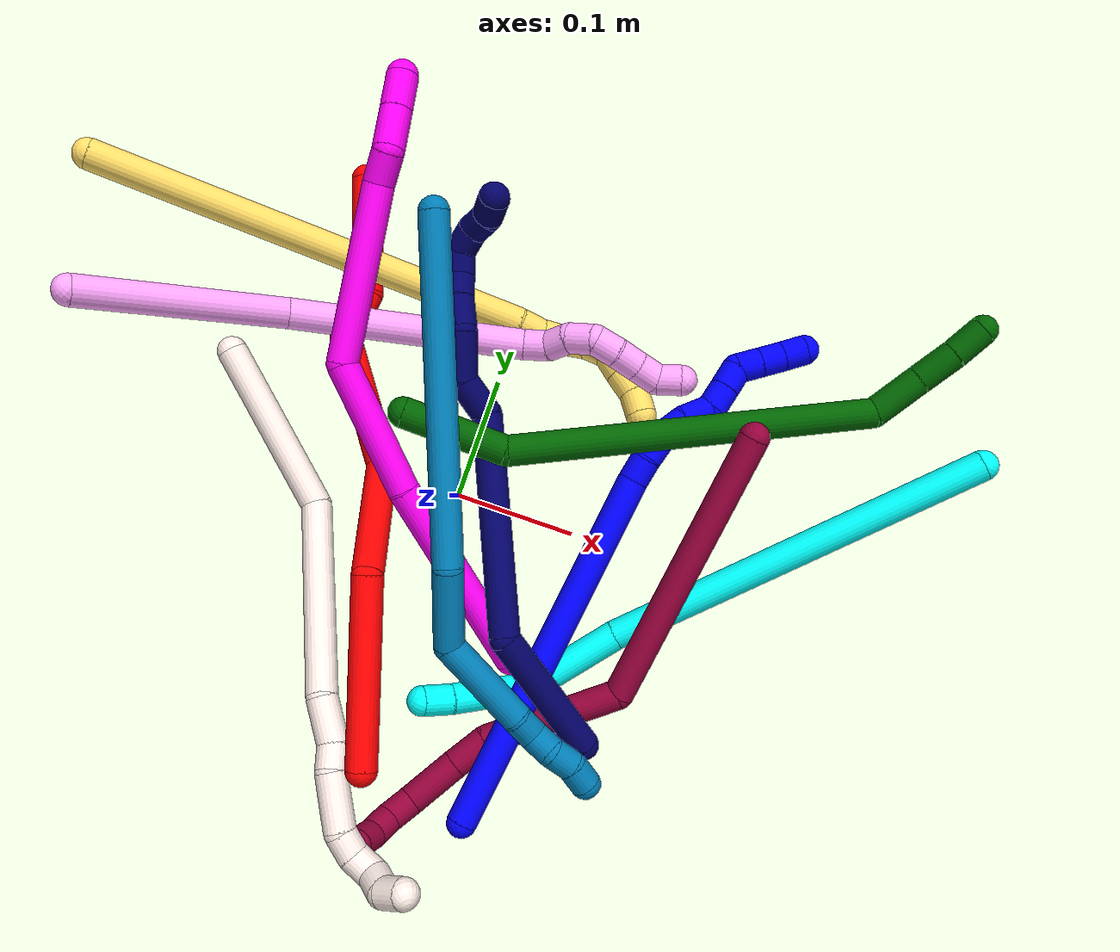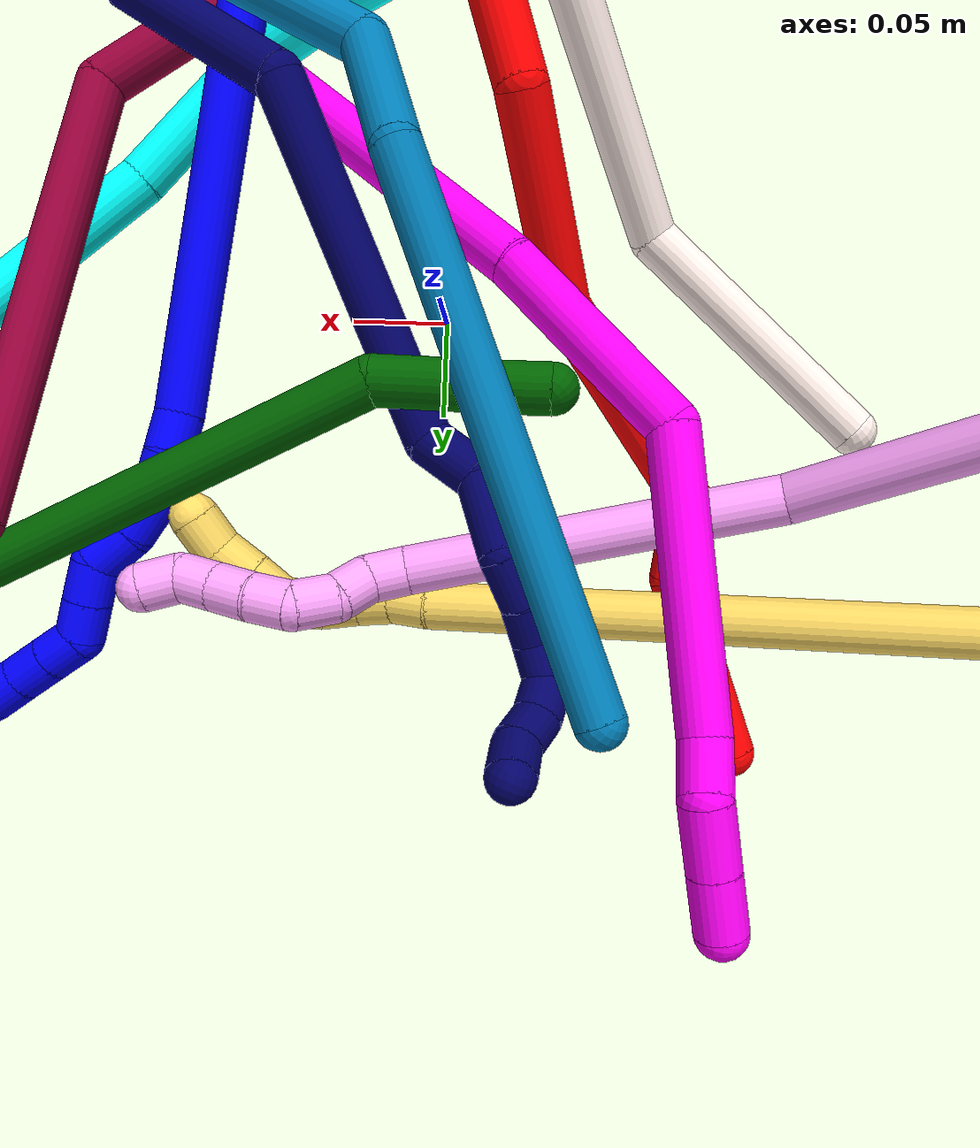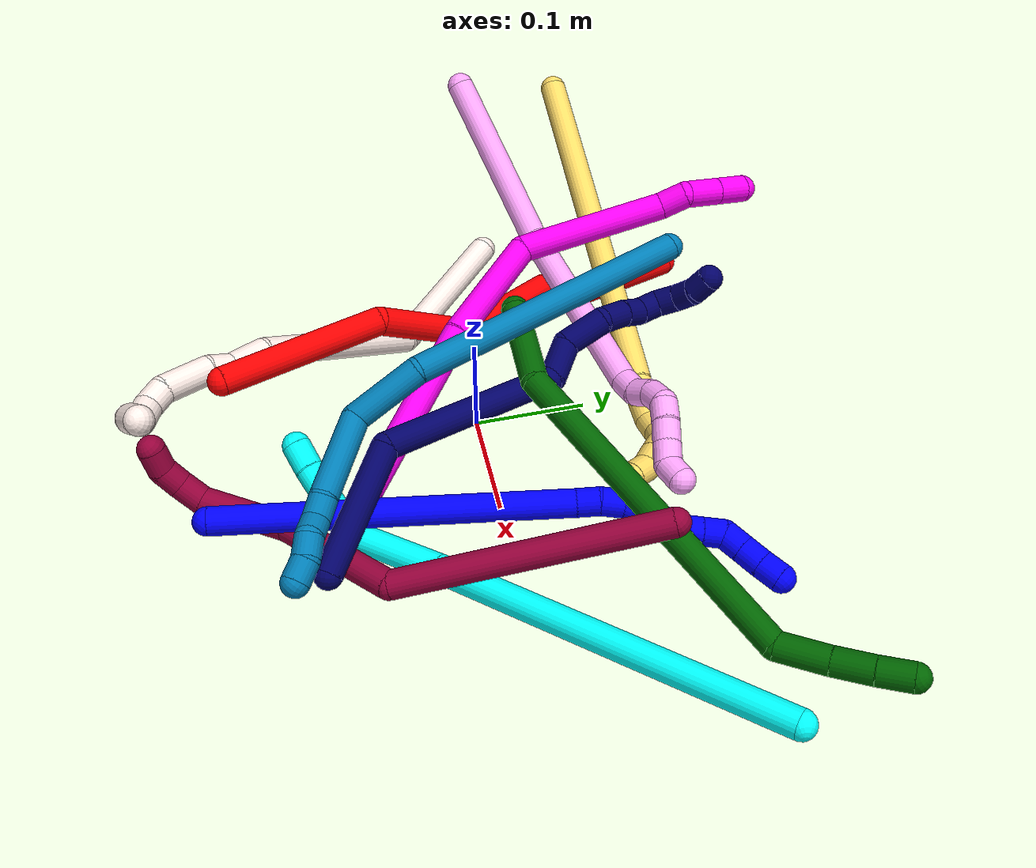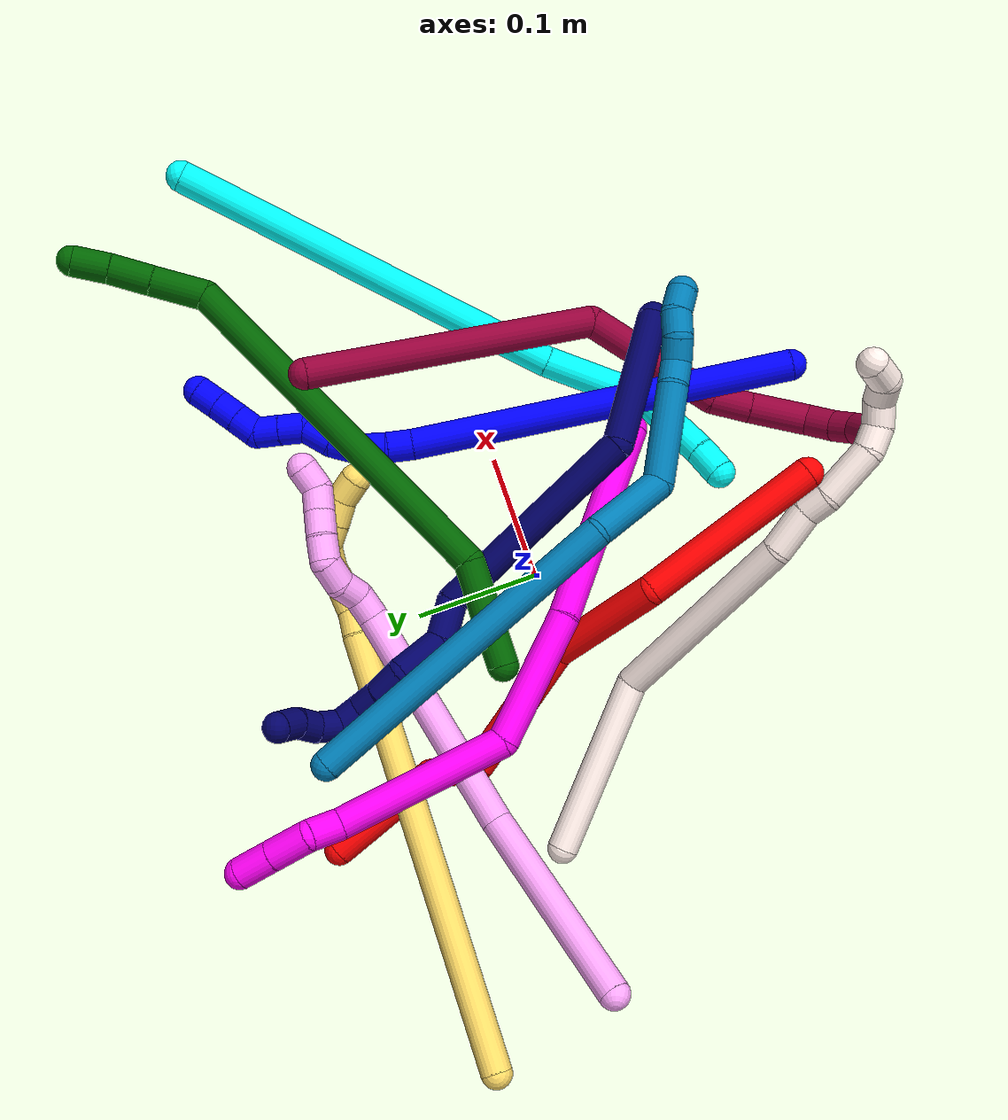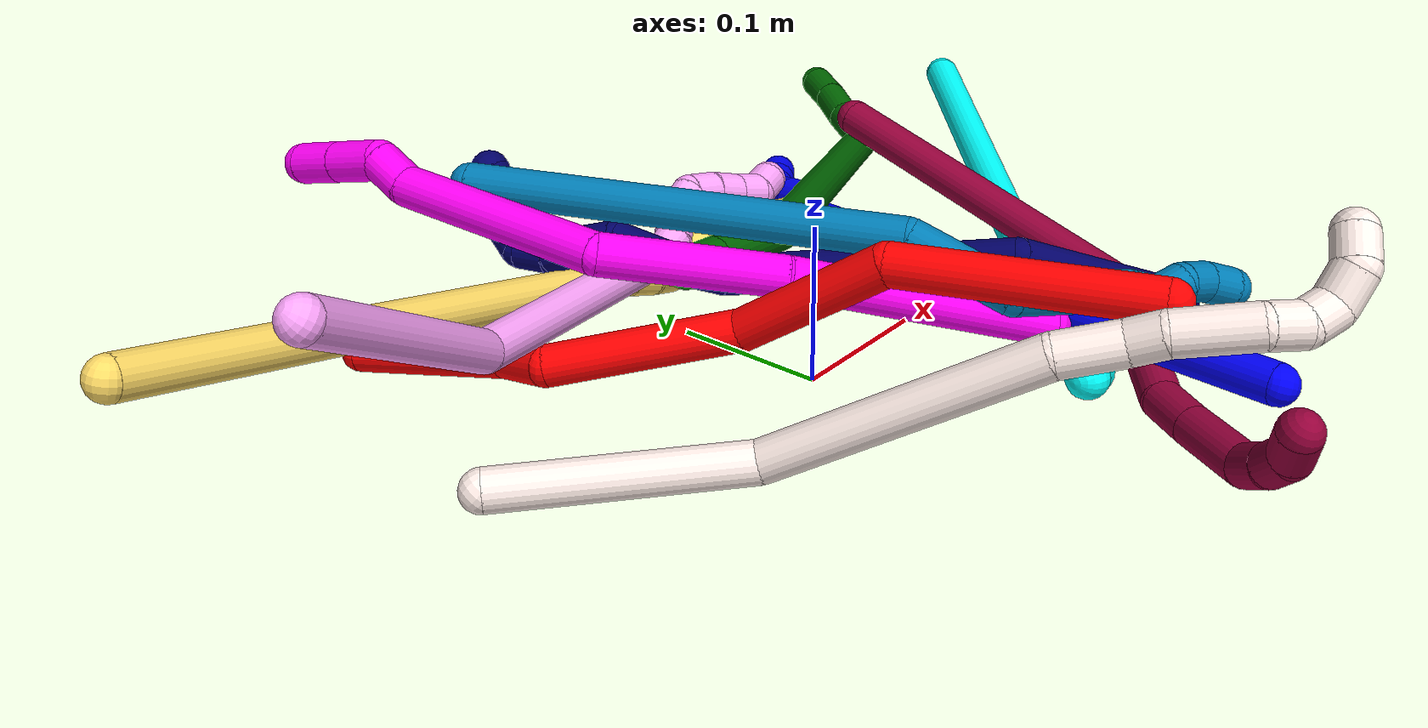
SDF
<sdf version="1.7">
 <world name="default">
  <plugin name="TubeGeneratorPlugin" filename="libtube_generator_plugin.so"/>
  <model name="photoneo_s_sensor">
   <static>1</static>
   <pose>0 0 2 1.57079 1.57079 3.14159</pose>
   <link name="link">
    <inertial><mass>0.1</mass></inertial>
    <sensor name="sensor" type="depth">
     <update_rate>30</update_rate>
     <camera>
      <horizontal_fov>1.22</horizontal_fov>
      <image><width>1920</width><height>1200</height><format>B8G8R8</format></image>
      <clip><near>0.1</near><far>4</far></clip>
      <depth_camera><output>points</output></depth_camera>
     </camera>
     <plugin name="camera_plugin" filename="libgazebo_ros_depth_camera.so">
      <baseline>0.2</baseline>
      <alwaysOn>1</alwaysOn>
      <updateRate>0.0</updateRate>
      <cameraName>camera_ir</cameraName>
      <imageTopicName>/camera/color/image_raw</imageTopicName>
      <cameraInfoTopicName>/camera/color/camera_info</cameraInfoTopicName>
      <depthImageTopicName>/camera/depth/image_raw</depthImageTopicName>
      <depthImageCameraInfoTopicName>/camera/depth/camera_info</depthImageCameraInfoTopicName>
      <pointCloudTopicName>/camera/depth/points</pointCloudTopicName>
      <frameName>fr_optical</frameName>
      <pointCloudCutoff>0.1</pointCloudCutoff>
      <pointCloudCutoffMax>2.0</pointCloudCutoffMax>
      <distortionK1>0</distortionK1>
      <distortionK2>0</distortionK2>
      <distortionK3>0</distortionK3>
      <distortionT1>0</distortionT1>
      <distortionT2>0</distortionT2>
      <CxPrime>0</CxPrime>
      <Cx>0</Cx>
      <Cy>0</Cy>
      <focalLength>0</focalLength>
      <hackBaseline>0</hackBaseline>
     </plugin>
    </sensor>
   </link>
  </model>
  <gravity>0 0 -9.8</gravity>
  <magnetic_field>6e-06 2.3e-05 -4.2e-05</magnetic_field>
  <atmosphere type="adiabatic"/>
  <physics name="default_physics" default="0" type="ode">
   <max_step_size>0.003</max_step_size>
   <real_time_factor>1</real_time_factor>
   <real_time_update_rate>1000</real_time_update_rate>
   <max_contacts>10000</max_contacts>
   <ode>
    <solver>
     <type>quick</type>
     <iters>100</iters>
     <sor>1.3</sor>
     <use_dynamic_moi_rescaling>0</use_dynamic_moi_rescaling>
    </solver>
    <constraints>
     <contact_max_correcting_vel>0</contact_max_correcting_vel>
     <contact_surface_layer>0.001</contact_surface_layer>
     <cfm>0</cfm>
     <erp>0.2</erp>
    </constraints>
   </ode>
  </physics>
  <scene><ambient>0.4 0.4 0.4 1</ambient><background>0.7 0.7 0.7 1</background><shadows>0</shadows></scene>
  <audio><device>default</device></audio>
  <spherical_coordinates>
   <surface_model>EARTH_WGS84</surface_model>
   <latitude_deg>0</latitude_deg>
   <longitude_deg>0</longitude_deg>
   <elevation>0</elevation>
   <heading_deg>0</heading_deg>
  </spherical_coordinates>
  <model name="bin">
   <static>1</static>
   <link name="bottom">
    <collision name="collision-bottom">
     <pose>0 0 -0.01 0 -0 0</pose>
     <geometry><box><size>0.8 0.6 0.02</size></box></geometry>
     <surface>
      <friction><ode><mu>100</mu><mu2>100</mu2></ode></friction>
      <contact><collide_bitmask>65535</collide_bitmask></contact>
     </surface>
    </collision>
   </link>
   <link name="west_wall">
    <collision name="collision-west_wall">
     <pose>-0.41 0 0.1 0 -0 0</pose>
     <geometry><box><size>0.02 0.6 0.2</size></box></geometry>
     <surface>
      <friction><ode><mu>100</mu><mu2>100</mu2></ode></friction>
      <contact><collide_bitmask>65535</collide_bitmask></contact>
     </surface>
    </collision>
   </link>
   <link name="east_wall">
    <collision name="collision-east_wall">
     <pose>0.41 0 0.1 0 -0 0</pose>
     <geometry><box><size>0.02 0.6 0.2</size></box></geometry>
     <surface>
      <friction><ode><mu>100</mu><mu2>100</mu2></ode></friction>
      <contact><collide_bitmask>65535</collide_bitmask></contact>
     </surface>
    </collision>
   </link>
   <link name="south_wall">
    <collision name="collision-south_wall">
     <pose>0 -0.31 0.1 0 -0 0</pose>
     <geometry><box><size>0.8 0.02 0.2</size></box></geometry>
     <surface>
      <friction><ode><mu>100</mu><mu2>100</mu2></ode></friction>
      <contact><collide_bitmask>65535</collide_bitmask></contact>
     </surface>
    </collision>
   </link>
   <link name="north_wall">
    <collision name="collision-north_wall">
     <pose>0 0.31 0.1 0 -0 0</pose>
     <geometry><box><size>0.8 0.02 0.2</size></box></geometry>
     <surface>
      <friction><ode><mu>100</mu><mu2>100</mu2></ode></friction>
      <contact><collide_bitmask>65535</collide_bitmask></contact>
     </surface>
    </collision>
   </link>
  </model>
  <model name="1">
   <static>0</static>
   <link name="1">
    <collision name="collision-cylinder-e_1_1_4">
     <pose>0.086936 0.073921 -0.103767 -2.52261 0.598793 -1.53551</pose>
     <geometry><cylinder><radius>0.0125</radius><length>0.308479</length></cylinder></geometry>
     <surface>
      <friction><ode><mu>1.16</mu><mu2>1.16</mu2><slip1>0</slip1><slip2>0</slip2></ode></friction>
      <contact><ode><kp>1e+06</kp><kd>1</kd><max_vel>0</max_vel><min_depth>0.001</min_depth></ode></contact>
     </surface>
    </collision>
    <visual name="visual-cylinder-e_1_1_4">
     <pose>0.086936 0.073921 -0.103767 -2.52261 0.598793 -1.53551</pose>
     <geometry><cylinder><radius>0.0125</radius><length>0.308479</length></cylinder></geometry>
     <material><ambient>0 0 1 1</ambient></material>
    </visual>
    <collision name="collision-cylinder-e_2_4_5">
     <pose>0.178797 0.154028 -0.214341 -2.40386 0.491513 -1.15116</pose>
     <geometry><cylinder><radius>0.0125</radius><length>0.020867</length></cylinder></geometry>
     <surface>
      <friction><ode><mu>1.16</mu><mu2>1.16</mu2><slip1>0</slip1><slip2>0</slip2></ode></friction>
      <contact><ode><kp>1e+06</kp><kd>1</kd><max_vel>0</max_vel><min_depth>0.001</min_depth></ode></contact>
     </surface>
    </collision>
    <visual name="visual-cylinder-e_2_4_5">
     <pose>0.178797 0.154028 -0.214341 -2.40386 0.491513 -1.15116</pose>
     <geometry><cylinder><radius>0.0125</radius><length>0.020867</length></cylinder></geometry>
     <material><ambient>0 0 1 1</ambient></material>
    </visual>
    <collision name="collision-cylinder-e_3_5_6">
     <pose>0.190608 0.166019 -0.226943 -2.35548 0.698456 -1.44135</pose>
     <geometry><cylinder><radius>0.0125</radius><length>0.021419</length></cylinder></geometry>
     <surface>
      <friction><ode><mu>1.16</mu><mu2>1.16</mu2><slip1>0</slip1><slip2>0</slip2></ode></friction>
      <contact><ode><kp>1e+06</kp><kd>1</kd><max_vel>0</max_vel><min_depth>0.001</min_depth></ode></contact>
     </surface>
    </collision>
    <visual name="visual-cylinder-e_3_5_6">
     <pose>0.190608 0.166019 -0.226943 -2.35548 0.698456 -1.44135</pose>
     <geometry><cylinder><radius>0.0125</radius><length>0.021419</length></cylinder></geometry>
     <material><ambient>0 0 1 1</ambient></material>
    </visual>
    <collision name="collision-cylinder-e_4_6_7">
     <pose>0.205592 0.180202 -0.236097 -1.95196 0.73118 -1.0298</pose>
     <geometry><cylinder><radius>0.0125</radius><length>0.024254</length></cylinder></geometry>
     <surface>
      <friction><ode><mu>1.16</mu><mu2>1.16</mu2><slip1>0</slip1><slip2>0</slip2></ode></friction>
      <contact><ode><kp>1e+06</kp><kd>1</kd><max_vel>0</max_vel><min_depth>0.001</min_depth></ode></contact>
     </surface>
    </collision>
    <visual name="visual-cylinder-e_4_6_7">
     <pose>0.205592 0.180202 -0.236097 -1.95196 0.73118 -1.0298</pose>
     <geometry><cylinder><radius>0.0125</radius><length>0.024254</length></cylinder></geometry>
     <material><ambient>0 0 1 1</ambient></material>
    </visual>
    <collision name="collision-cylinder-e_5_7_8">
     <pose>0.220832 0.19812 -0.240018 -1.62976 0.641848 -0.678007</pose>
     <geometry><cylinder><radius>0.0125</radius><length>0.023859</length></cylinder></geometry>
     <surface>
      <friction><ode><mu>1.16</mu><mu2>1.16</mu2><slip1>0</slip1><slip2>0</slip2></ode></friction>
      <contact><ode><kp>1e+06</kp><kd>1</kd><max_vel>0</max_vel><min_depth>0.001</min_depth></ode></contact>
     </surface>
    </collision>
    <visual name="visual-cylinder-e_5_7_8">
     <pose>0.220832 0.19812 -0.240018 -1.62976 0.641848 -0.678007</pose>
     <geometry><cylinder><radius>0.0125</radius><length>0.023859</length></cylinder></geometry>
     <material><ambient>0 0 1 1</ambient></material>
    </visual>
    <collision name="collision-cylinder-e_6_8_9">
     <pose>0.23509 0.212753 -0.24636 -2.41909 0.745778 -1.60553</pose>
     <geometry><cylinder><radius>0.0125</radius><length>0.020976</length></cylinder></geometry>
     <surface>
      <friction><ode><mu>1.16</mu><mu2>1.16</mu2><slip1>0</slip1><slip2>0</slip2></ode></friction>
      <contact><ode><kp>1e+06</kp><kd>1</kd><max_vel>0</max_vel><min_depth>0.001</min_depth></ode></contact>
     </surface>
    </collision>
    <visual name="visual-cylinder-e_6_8_9">
     <pose>0.23509 0.212753 -0.24636 -2.41909 0.745778 -1.60553</pose>
     <geometry><cylinder><radius>0.0125</radius><length>0.020976</length></cylinder></geometry>
     <material><ambient>0 0 1 1</ambient></material>
    </visual>
    <collision name="collision-cylinder-e_7_9_10">
     <pose>0.249075 0.222603 -0.257753 -2.43873 0.751002 -1.64319</pose>
     <geometry><cylinder><radius>0.0125</radius><length>0.02013</length></cylinder></geometry>
     <surface>
      <friction><ode><mu>1.16</mu><mu2>1.16</mu2><slip1>0</slip1><slip2>0</slip2></ode></friction>
      <contact><ode><kp>1e+06</kp><kd>1</kd><max_vel>0</max_vel><min_depth>0.001</min_depth></ode></contact>
     </surface>
    </collision>
    <visual name="visual-cylinder-e_7_9_10">
     <pose>0.249075 0.222603 -0.257753 -2.43873 0.751002 -1.64319</pose>
     <geometry><cylinder><radius>0.0125</radius><length>0.02013</length></cylinder></geometry>
     <material><ambient>0 0 1 1</ambient></material>
    </visual>
    <collision name="collision-cylinder-e_8_10_11">
     <pose>0.262315 0.235024 -0.262526 -1.46153 0.690584 -0.623754</pose>
     <geometry><cylinder><radius>0.0125</radius><length>0.020006</length></cylinder></geometry>
     <surface>
      <friction><ode><mu>1.16</mu><mu2>1.16</mu2><slip1>0</slip1><slip2>0</slip2></ode></friction>
      <contact><ode><kp>1e+06</kp><kd>1</kd><max_vel>0</max_vel><min_depth>0.001</min_depth></ode></contact>
     </surface>
    </collision>
    <visual name="visual-cylinder-e_8_10_11">
     <pose>0.262315 0.235024 -0.262526 -1.46153 0.690584 -0.623754</pose>
     <geometry><cylinder><radius>0.0125</radius><length>0.020006</length></cylinder></geometry>
     <material><ambient>0 0 1 1</ambient></material>
    </visual>
    <collision name="collision-cylinder-e_9_11_12">
     <pose>0.275085 0.250338 -0.260872 -1.46486 0.693881 -0.628746</pose>
     <geometry><cylinder><radius>0.0125</radius><length>0.02001</length></cylinder></geometry>
     <surface>
      <friction><ode><mu>1.16</mu><mu2>1.16</mu2><slip1>0</slip1><slip2>0</slip2></ode></friction>
      <contact><ode><kp>1e+06</kp><kd>1</kd><max_vel>0</max_vel><min_depth>0.001</min_depth></ode></contact>
     </surface>
    </collision>
    <visual name="visual-cylinder-e_9_11_12">
     <pose>0.275085 0.250338 -0.260872 -1.46486 0.693881 -0.628746</pose>
     <geometry><cylinder><radius>0.0125</radius><length>0.02001</length></cylinder></geometry>
     <material><ambient>0 0 1 1</ambient></material>
    </visual>
    <collision name="collision-cylinder-e_10_12_2">
     <pose>0.287603 0.265879 -0.259544 -1.50573 0.658471 -0.619649</pose>
     <geometry><cylinder><radius>0.0125</radius><length>0.02</length></cylinder></geometry>
     <surface>
      <friction><ode><mu>1.16</mu><mu2>1.16</mu2><slip1>0</slip1><slip2>0</slip2></ode></friction>
      <contact><ode><kp>1e+06</kp><kd>1</kd><max_vel>0</max_vel><min_depth>0.001</min_depth></ode></contact>
     </surface>
    </collision>
    <visual name="visual-cylinder-e_10_12_2">
     <pose>0.287603 0.265879 -0.259544 -1.50573 0.658471 -0.619649</pose>
     <geometry><cylinder><radius>0.0125</radius><length>0.02</length></cylinder></geometry>
     <material><ambient>0 0 1 1</ambient></material>
    </visual>
    <collision name="collision-sphere-2">
     <pose>0.293722 0.273771 -0.25903 0 -0 0</pose>
     <geometry><sphere><radius>0.0125</radius></sphere></geometry>
     <surface>
      <friction><ode><mu>1.16</mu><mu2>1.16</mu2><slip1>0</slip1><slip2>0</slip2></ode></friction>
      <contact><ode><kp>1e+06</kp><kd>1</kd><max_vel>0</max_vel><min_depth>0.001</min_depth></ode></contact>
     </surface>
    </collision>
    <visual name="visual-sphere-2">
     <pose>0.293722 0.273771 -0.25903 0 -0 0</pose>
     <geometry><sphere><radius>0.0125</radius></sphere></geometry>
     <material><ambient>0 0 1 1</ambient></material>
    </visual>
    <collision name="collision-sphere-12">
     <pose>0.281484 0.257986 -0.260059 0 -0 0</pose>
     <geometry><sphere><radius>0.0125</radius></sphere></geometry>
     <surface>
      <friction><ode><mu>1.16</mu><mu2>1.16</mu2><slip1>0</slip1><slip2>0</slip2></ode></friction>
      <contact><ode><kp>1e+06</kp><kd>1</kd><max_vel>0</max_vel><min_depth>0.001</min_depth></ode></contact>
     </surface>
    </collision>
    <visual name="visual-sphere-12">
     <pose>0.281484 0.257986 -0.260059 0 -0 0</pose>
     <geometry><sphere><radius>0.0125</radius></sphere></geometry>
     <material><ambient>0 0 1 1</ambient></material>
    </visual>
    <collision name="collision-sphere-11">
     <pose>0.268686 0.242689 -0.261685 0 -0 0</pose>
     <geometry><sphere><radius>0.0125</radius></sphere></geometry>
     <surface>
      <friction><ode><mu>1.16</mu><mu2>1.16</mu2><slip1>0</slip1><slip2>0</slip2></ode></friction>
      <contact><ode><kp>1e+06</kp><kd>1</kd><max_vel>0</max_vel><min_depth>0.001</min_depth></ode></contact>
     </surface>
    </collision>
    <visual name="visual-sphere-11">
     <pose>0.268686 0.242689 -0.261685 0 -0 0</pose>
     <geometry><sphere><radius>0.0125</radius></sphere></geometry>
     <material><ambient>0 0 1 1</ambient></material>
    </visual>
    <collision name="collision-sphere-10">
     <pose>0.255943 0.227359 -0.263367 0 -0 0</pose>
     <geometry><sphere><radius>0.0125</radius></sphere></geometry>
     <surface>
      <friction><ode><mu>1.16</mu><mu2>1.16</mu2><slip1>0</slip1><slip2>0</slip2></ode></friction>
      <contact><ode><kp>1e+06</kp><kd>1</kd><max_vel>0</max_vel><min_depth>0.001</min_depth></ode></contact>
     </surface>
    </collision>
    <visual name="visual-sphere-10">
     <pose>0.255943 0.227359 -0.263367 0 -0 0</pose>
     <geometry><sphere><radius>0.0125</radius></sphere></geometry>
     <material><ambient>0 0 1 1</ambient></material>
    </visual>
    <collision name="collision-sphere-9">
     <pose>0.242207 0.217847 -0.252139 0 -0 0</pose>
     <geometry><sphere><radius>0.0125</radius></sphere></geometry>
     <surface>
      <friction><ode><mu>1.16</mu><mu2>1.16</mu2><slip1>0</slip1><slip2>0</slip2></ode></friction>
      <contact><ode><kp>1e+06</kp><kd>1</kd><max_vel>0</max_vel><min_depth>0.001</min_depth></ode></contact>
     </surface>
    </collision>
    <visual name="visual-sphere-9">
     <pose>0.242207 0.217847 -0.252139 0 -0 0</pose>
     <geometry><sphere><radius>0.0125</radius></sphere></geometry>
     <material><ambient>0 0 1 1</ambient></material>
    </visual>
    <collision name="collision-sphere-4">
     <pose>0.173873 0.147841 -0.207534 0 -0 0</pose>
     <geometry><sphere><radius>0.0125</radius></sphere></geometry>
     <surface>
      <friction><ode><mu>1.16</mu><mu2>1.16</mu2><slip1>0</slip1><slip2>0</slip2></ode></friction>
      <contact><ode><kp>1e+06</kp><kd>1</kd><max_vel>0</max_vel><min_depth>0.001</min_depth></ode></contact>
     </surface>
    </collision>
    <visual name="visual-sphere-4">
     <pose>0.173873 0.147841 -0.207534 0 -0 0</pose>
     <geometry><sphere><radius>0.0125</radius></sphere></geometry>
     <material><ambient>0 0 1 1</ambient></material>
    </visual>
    <collision name="collision-sphere-1">
     <geometry><sphere><radius>0.0125</radius></sphere></geometry>
     <surface>
      <friction><ode><mu>1.16</mu><mu2>1.16</mu2><slip1>0</slip1><slip2>0</slip2></ode></friction>
      <contact><ode><kp>1e+06</kp><kd>1</kd><max_vel>0</max_vel><min_depth>0.001</min_depth></ode></contact>
     </surface>
    </collision>
    <visual name="visual-sphere-1">
     <geometry><sphere><radius>0.0125</radius></sphere></geometry>
     <material><ambient>0 0 1 1</ambient></material>
    </visual>
    <collision name="collision-sphere-8">
     <pose>0.227974 0.207658 -0.240581 0 -0 0</pose>
     <geometry><sphere><radius>0.0125</radius></sphere></geometry>
     <surface>
      <friction><ode><mu>1.16</mu><mu2>1.16</mu2><slip1>0</slip1><slip2>0</slip2></ode></friction>
      <contact><ode><kp>1e+06</kp><kd>1</kd><max_vel>0</max_vel><min_depth>0.001</min_depth></ode></contact>
     </surface>
    </collision>
    <visual name="visual-sphere-8">
     <pose>0.227974 0.207658 -0.240581 0 -0 0</pose>
     <geometry><sphere><radius>0.0125</radius></sphere></geometry>
     <material><ambient>0 0 1 1</ambient></material>
    </visual>
    <collision name="collision-sphere-5">
     <pose>0.183721 0.160215 -0.221148 0 -0 0</pose>
     <geometry><sphere><radius>0.0125</radius></sphere></geometry>
     <surface>
      <friction><ode><mu>1.16</mu><mu2>1.16</mu2><slip1>0</slip1><slip2>0</slip2></ode></friction>
      <contact><ode><kp>1e+06</kp><kd>1</kd><max_vel>0</max_vel><min_depth>0.001</min_depth></ode></contact>
     </surface>
    </collision>
    <visual name="visual-sphere-5">
     <pose>0.183721 0.160215 -0.221148 0 -0 0</pose>
     <geometry><sphere><radius>0.0125</radius></sphere></geometry>
     <material><ambient>0 0 1 1</ambient></material>
    </visual>
    <collision name="collision-sphere-6">
     <pose>0.197495 0.171822 -0.232738 0 -0 0</pose>
     <geometry><sphere><radius>0.0125</radius></sphere></geometry>
     <surface>
      <friction><ode><mu>1.16</mu><mu2>1.16</mu2><slip1>0</slip1><slip2>0</slip2></ode></friction>
      <contact><ode><kp>1e+06</kp><kd>1</kd><max_vel>0</max_vel><min_depth>0.001</min_depth></ode></contact>
     </surface>
    </collision>
    <visual name="visual-sphere-6">
     <pose>0.197495 0.171822 -0.232738 0 -0 0</pose>
     <geometry><sphere><radius>0.0125</radius></sphere></geometry>
     <material><ambient>0 0 1 1</ambient></material>
    </visual>
    <collision name="collision-sphere-7">
     <pose>0.21369 0.188581 -0.239455 0 -0 0</pose>
     <geometry><sphere><radius>0.0125</radius></sphere></geometry>
     <surface>
      <friction><ode><mu>1.16</mu><mu2>1.16</mu2><slip1>0</slip1><slip2>0</slip2></ode></friction>
      <contact><ode><kp>1e+06</kp><kd>1</kd><max_vel>0</max_vel><min_depth>0.001</min_depth></ode></contact>
     </surface>
    </collision>
    <visual name="visual-sphere-7">
     <pose>0.21369 0.188581 -0.239455 0 -0 0</pose>
     <geometry><sphere><radius>0.0125</radius></sphere></geometry>
     <material><ambient>0 0 1 1</ambient></material>
    </visual>
    <inertial>
     <pose>0.142673 0.125286 -0.157631 0 -0 0</pose>
     <mass>0.5</mass>
     <inertia>
      <ixx>-0.001938</ixx>
      <ixy>0</ixy>
      <ixz>0</ixz>
      <iyy>-0.001279</iyy>
      <iyz>0</iyz>
      <izz>-0.002603</izz>
     </inertia>
    </inertial>
   </link>
   <pose>0.091416 -0.246867 0.042864 2.02371 0.952592 1.03103</pose>
  </model>
  <model name="2">
   <static>0</static>
   <link name="2">
    <collision name="collision-cylinder-e_1_1_4">
     <pose>-0.019781 0.070378 0.004434 -1.50787 -0.273477 0.256977</pose>
     <geometry><cylinder><radius>0.0125</radius><length>0.146479</length></cylinder></geometry>
     <surface>
      <friction><ode><mu>1.16</mu><mu2>1.16</mu2><slip1>0</slip1><slip2>0</slip2></ode></friction>
      <contact><ode><kp>1e+06</kp><kd>1</kd><max_vel>0</max_vel><min_depth>0.001</min_depth></ode></contact>
     </surface>
    </collision>
    <visual name="visual-cylinder-e_1_1_4">
     <pose>-0.019781 0.070378 0.004434 -1.50787 -0.273477 0.256977</pose>
     <geometry><cylinder><radius>0.0125</radius><length>0.146479</length></cylinder></geometry>
     <material><ambient>1 0 0 1</ambient></material>
    </visual>
    <collision name="collision-cylinder-e_2_4_5">
     <pose>-0.044773 0.181799 0.037349 -0.964153 -0.103941 0.054423</pose>
     <geometry><cylinder><radius>0.0125</radius><length>0.100455</length></cylinder></geometry>
     <surface>
      <friction><ode><mu>1.16</mu><mu2>1.16</mu2><slip1>0</slip1><slip2>0</slip2></ode></friction>
      <contact><ode><kp>1e+06</kp><kd>1</kd><max_vel>0</max_vel><min_depth>0.001</min_depth></ode></contact>
     </surface>
    </collision>
    <visual name="visual-cylinder-e_2_4_5">
     <pose>-0.044773 0.181799 0.037349 -0.964153 -0.103941 0.054423</pose>
     <geometry><cylinder><radius>0.0125</radius><length>0.100455</length></cylinder></geometry>
     <material><ambient>1 0 0 1</ambient></material>
    </visual>
    <collision name="collision-cylinder-e_3_5_6">
     <pose>-0.044521 0.278883 0.074934 -1.40976 0.095913 -0.081607</pose>
     <geometry><cylinder><radius>0.0125</radius><length>0.114077</length></cylinder></geometry>
     <surface>
      <friction><ode><mu>1.16</mu><mu2>1.16</mu2><slip1>0</slip1><slip2>0</slip2></ode></friction>
      <contact><ode><kp>1e+06</kp><kd>1</kd><max_vel>0</max_vel><min_depth>0.001</min_depth></ode></contact>
     </surface>
    </collision>
    <visual name="visual-cylinder-e_3_5_6">
     <pose>-0.044521 0.278883 0.074934 -1.40976 0.095913 -0.081607</pose>
     <geometry><cylinder><radius>0.0125</radius><length>0.114077</length></cylinder></geometry>
     <material><ambient>1 0 0 1</ambient></material>
    </visual>
    <collision name="collision-cylinder-e_4_6_7">
     <pose>-0.050407 0.350249 0.091607 -1.11198 -0.586084 0.370672</pose>
     <geometry><cylinder><radius>0.0125</radius><length>0.041032</length></cylinder></geometry>
     <surface>
      <friction><ode><mu>1.16</mu><mu2>1.16</mu2><slip1>0</slip1><slip2>0</slip2></ode></friction>
      <contact><ode><kp>1e+06</kp><kd>1</kd><max_vel>0</max_vel><min_depth>0.001</min_depth></ode></contact>
     </surface>
    </collision>
    <visual name="visual-cylinder-e_4_6_7">
     <pose>-0.050407 0.350249 0.091607 -1.11198 -0.586084 0.370672</pose>
     <geometry><cylinder><radius>0.0125</radius><length>0.041032</length></cylinder></geometry>
     <material><ambient>1 0 0 1</ambient></material>
    </visual>
    <collision name="collision-cylinder-e_5_7_2">
     <pose>-0.071185 0.413183 0.10576 -1.43339 -0.193764 0.168941</pose>
     <geometry><cylinder><radius>0.0125</radius><length>0.097957</length></cylinder></geometry>
     <surface>
      <friction><ode><mu>1.16</mu><mu2>1.16</mu2><slip1>0</slip1><slip2>0</slip2></ode></friction>
      <contact><ode><kp>1e+06</kp><kd>1</kd><max_vel>0</max_vel><min_depth>0.001</min_depth></ode></contact>
     </surface>
    </collision>
    <visual name="visual-cylinder-e_5_7_2">
     <pose>-0.071185 0.413183 0.10576 -1.43339 -0.193764 0.168941</pose>
     <geometry><cylinder><radius>0.0125</radius><length>0.097957</length></cylinder></geometry>
     <material><ambient>1 0 0 1</ambient></material>
    </visual>
    <collision name="collision-sphere-2">
     <pose>-0.080616 0.460792 0.112344 0 -0 0</pose>
     <geometry><sphere><radius>0.0125</radius></sphere></geometry>
     <surface>
      <friction><ode><mu>1.16</mu><mu2>1.16</mu2><slip1>0</slip1><slip2>0</slip2></ode></friction>
      <contact><ode><kp>1e+06</kp><kd>1</kd><max_vel>0</max_vel><min_depth>0.001</min_depth></ode></contact>
     </surface>
    </collision>
    <visual name="visual-sphere-2">
     <pose>-0.080616 0.460792 0.112344 0 -0 0</pose>
     <geometry><sphere><radius>0.0125</radius></sphere></geometry>
     <material><ambient>1 0 0 1</ambient></material>
    </visual>
    <collision name="collision-sphere-7">
     <pose>-0.061754 0.365574 0.099177 0 -0 0</pose>
     <geometry><sphere><radius>0.0125</radius></sphere></geometry>
     <surface>
      <friction><ode><mu>1.16</mu><mu2>1.16</mu2><slip1>0</slip1><slip2>0</slip2></ode></friction>
      <contact><ode><kp>1e+06</kp><kd>1</kd><max_vel>0</max_vel><min_depth>0.001</min_depth></ode></contact>
     </surface>
    </collision>
    <visual name="visual-sphere-7">
     <pose>-0.061754 0.365574 0.099177 0 -0 0</pose>
     <geometry><sphere><radius>0.0125</radius></sphere></geometry>
     <material><ambient>1 0 0 1</ambient></material>
    </visual>
    <collision name="collision-sphere-6">
     <pose>-0.039059 0.334925 0.084037 0 -0 0</pose>
     <geometry><sphere><radius>0.0125</radius></sphere></geometry>
     <surface>
      <friction><ode><mu>1.16</mu><mu2>1.16</mu2><slip1>0</slip1><slip2>0</slip2></ode></friction>
      <contact><ode><kp>1e+06</kp><kd>1</kd><max_vel>0</max_vel><min_depth>0.001</min_depth></ode></contact>
     </surface>
    </collision>
    <visual name="visual-sphere-6">
     <pose>-0.039059 0.334925 0.084037 0 -0 0</pose>
     <geometry><sphere><radius>0.0125</radius></sphere></geometry>
     <material><ambient>1 0 0 1</ambient></material>
    </visual>
    <collision name="collision-sphere-5">
     <pose>-0.049984 0.222842 0.06583 0 -0 0</pose>
     <geometry><sphere><radius>0.0125</radius></sphere></geometry>
     <surface>
      <friction><ode><mu>1.16</mu><mu2>1.16</mu2><slip1>0</slip1><slip2>0</slip2></ode></friction>
      <contact><ode><kp>1e+06</kp><kd>1</kd><max_vel>0</max_vel><min_depth>0.001</min_depth></ode></contact>
     </surface>
    </collision>
    <visual name="visual-sphere-5">
     <pose>-0.049984 0.222842 0.06583 0 -0 0</pose>
     <geometry><sphere><radius>0.0125</radius></sphere></geometry>
     <material><ambient>1 0 0 1</ambient></material>
    </visual>
    <collision name="collision-sphere-1">
     <geometry><sphere><radius>0.0125</radius></sphere></geometry>
     <surface>
      <friction><ode><mu>1.16</mu><mu2>1.16</mu2><slip1>0</slip1><slip2>0</slip2></ode></friction>
      <contact><ode><kp>1e+06</kp><kd>1</kd><max_vel>0</max_vel><min_depth>0.001</min_depth></ode></contact>
     </surface>
    </collision>
    <visual name="visual-sphere-1">
     <geometry><sphere><radius>0.0125</radius></sphere></geometry>
     <material><ambient>1 0 0 1</ambient></material>
    </visual>
    <collision name="collision-sphere-4">
     <pose>-0.039561 0.140757 0.008869 0 -0 0</pose>
     <geometry><sphere><radius>0.0125</radius></sphere></geometry>
     <surface>
      <friction><ode><mu>1.16</mu><mu2>1.16</mu2><slip1>0</slip1><slip2>0</slip2></ode></friction>
      <contact><ode><kp>1e+06</kp><kd>1</kd><max_vel>0</max_vel><min_depth>0.001</min_depth></ode></contact>
     </surface>
    </collision>
    <visual name="visual-sphere-4">
     <pose>-0.039561 0.140757 0.008869 0 -0 0</pose>
     <geometry><sphere><radius>0.0125</radius></sphere></geometry>
     <material><ambient>1 0 0 1</ambient></material>
    </visual>
    <inertial>
     <pose>-0.043031 0.230463 0.054137 0 -0 0</pose>
     <mass>0.5</mass>
     <inertia>
      <ixx>0.000619</ixx>
      <ixy>0</ixy>
      <ixz>0</ixz>
      <iyy>0.000237</iyy>
      <iyz>0</iyz>
      <izz>-0.000443</izz>
     </inertia>
    </inertial>
   </link>
   <pose>0.006303 -0.215754 0.116482 -3.10253 0.261485 -2.54393</pose>
  </model>
  <model name="3">
   <static>0</static>
   <link name="3">
    <collision name="collision-cylinder-e_1_1_4">
     <pose>-0.093819 -0.087201 -0.099148 2.42022 -0.617763 -1.40431</pose>
     <geometry><cylinder><radius>0.0125</radius><length>0.323954</length></cylinder></geometry>
     <surface>
      <friction><ode><mu>1.16</mu><mu2>1.16</mu2><slip1>0</slip1><slip2>0</slip2></ode></friction>
      <contact><ode><kp>1e+06</kp><kd>1</kd><max_vel>0</max_vel><min_depth>0.001</min_depth></ode></contact>
     </surface>
    </collision>
    <visual name="visual-cylinder-e_1_1_4">
     <pose>-0.093819 -0.087201 -0.099148 2.42022 -0.617763 -1.40431</pose>
     <geometry><cylinder><radius>0.0125</radius><length>0.323954</length></cylinder></geometry>
     <material><ambient>0.003922 1 0.996078 1</ambient></material>
    </visual>
    <collision name="collision-cylinder-e_2_4_5">
     <pose>-0.2165 -0.194679 -0.221045 2.41358 -0.758255 -1.61549</pose>
     <geometry><cylinder><radius>0.0125</radius><length>0.083943</length></cylinder></geometry>
     <surface>
      <friction><ode><mu>1.16</mu><mu2>1.16</mu2><slip1>0</slip1><slip2>0</slip2></ode></friction>
      <contact><ode><kp>1e+06</kp><kd>1</kd><max_vel>0</max_vel><min_depth>0.001</min_depth></ode></contact>
     </surface>
    </collision>
    <visual name="visual-cylinder-e_2_4_5">
     <pose>-0.2165 -0.194679 -0.221045 2.41358 -0.758255 -1.61549</pose>
     <geometry><cylinder><radius>0.0125</radius><length>0.083943</length></cylinder></geometry>
     <material><ambient>0.003922 1 0.996078 1</ambient></material>
    </visual>
    <collision name="collision-cylinder-e_3_5_6">
     <pose>-0.256812 -0.213966 -0.260256 -3.08158 -0.60682 2.95042</pose>
     <geometry><cylinder><radius>0.0125</radius><length>0.040155</length></cylinder></geometry>
     <surface>
      <friction><ode><mu>1.16</mu><mu2>1.16</mu2><slip1>0</slip1><slip2>0</slip2></ode></friction>
      <contact><ode><kp>1e+06</kp><kd>1</kd><max_vel>0</max_vel><min_depth>0.001</min_depth></ode></contact>
     </surface>
    </collision>
    <visual name="visual-cylinder-e_3_5_6">
     <pose>-0.256812 -0.213966 -0.260256 -3.08158 -0.60682 2.95042</pose>
     <geometry><cylinder><radius>0.0125</radius><length>0.040155</length></cylinder></geometry>
     <material><ambient>0.003922 1 0.996078 1</ambient></material>
    </visual>
    <collision name="collision-cylinder-e_4_6_7">
     <pose>-0.276294 -0.211985 -0.288061 -3.05433 -0.614493 2.86812</pose>
     <geometry><cylinder><radius>0.0125</radius><length>0.027867</length></cylinder></geometry>
     <surface>
      <friction><ode><mu>1.16</mu><mu2>1.16</mu2><slip1>0</slip1><slip2>0</slip2></ode></friction>
      <contact><ode><kp>1e+06</kp><kd>1</kd><max_vel>0</max_vel><min_depth>0.001</min_depth></ode></contact>
     </surface>
    </collision>
    <visual name="visual-cylinder-e_4_6_7">
     <pose>-0.276294 -0.211985 -0.288061 -3.05433 -0.614493 2.86812</pose>
     <geometry><cylinder><radius>0.0125</radius><length>0.027867</length></cylinder></geometry>
     <material><ambient>0.003922 1 0.996078 1</ambient></material>
    </visual>
    <collision name="collision-cylinder-e_5_7_2">
     <pose>-0.290329 -0.210302 -0.309817 -3.07535 -0.521798 2.89463</pose>
     <geometry><cylinder><radius>0.0125</radius><length>0.024081</length></cylinder></geometry>
     <surface>
      <friction><ode><mu>1.16</mu><mu2>1.16</mu2><slip1>0</slip1><slip2>0</slip2></ode></friction>
      <contact><ode><kp>1e+06</kp><kd>1</kd><max_vel>0</max_vel><min_depth>0.001</min_depth></ode></contact>
     </surface>
    </collision>
    <visual name="visual-cylinder-e_5_7_2">
     <pose>-0.290329 -0.210302 -0.309817 -3.07535 -0.521798 2.89463</pose>
     <geometry><cylinder><radius>0.0125</radius><length>0.024081</length></cylinder></geometry>
     <material><ambient>0.003922 1 0.996078 1</ambient></material>
    </visual>
    <collision name="collision-sphere-2">
     <pose>-0.296331 -0.209611 -0.320232 0 -0 0</pose>
     <geometry><sphere><radius>0.0125</radius></sphere></geometry>
     <surface>
      <friction><ode><mu>1.16</mu><mu2>1.16</mu2><slip1>0</slip1><slip2>0</slip2></ode></friction>
      <contact><ode><kp>1e+06</kp><kd>1</kd><max_vel>0</max_vel><min_depth>0.001</min_depth></ode></contact>
     </surface>
    </collision>
    <visual name="visual-sphere-2">
     <pose>-0.296331 -0.209611 -0.320232 0 -0 0</pose>
     <geometry><sphere><radius>0.0125</radius></sphere></geometry>
     <material><ambient>0.003922 1 0.996078 1</ambient></material>
    </visual>
    <collision name="collision-sphere-7">
     <pose>-0.284328 -0.210993 -0.299402 0 -0 0</pose>
     <geometry><sphere><radius>0.0125</radius></sphere></geometry>
     <surface>
      <friction><ode><mu>1.16</mu><mu2>1.16</mu2><slip1>0</slip1><slip2>0</slip2></ode></friction>
      <contact><ode><kp>1e+06</kp><kd>1</kd><max_vel>0</max_vel><min_depth>0.001</min_depth></ode></contact>
     </surface>
    </collision>
    <visual name="visual-sphere-7">
     <pose>-0.284328 -0.210993 -0.299402 0 -0 0</pose>
     <geometry><sphere><radius>0.0125</radius></sphere></geometry>
     <material><ambient>0.003922 1 0.996078 1</ambient></material>
    </visual>
    <collision name="collision-sphere-6">
     <pose>-0.268261 -0.212977 -0.276719 0 -0 0</pose>
     <geometry><sphere><radius>0.0125</radius></sphere></geometry>
     <surface>
      <friction><ode><mu>1.16</mu><mu2>1.16</mu2><slip1>0</slip1><slip2>0</slip2></ode></friction>
      <contact><ode><kp>1e+06</kp><kd>1</kd><max_vel>0</max_vel><min_depth>0.001</min_depth></ode></contact>
     </surface>
    </collision>
    <visual name="visual-sphere-6">
     <pose>-0.268261 -0.212977 -0.276719 0 -0 0</pose>
     <geometry><sphere><radius>0.0125</radius></sphere></geometry>
     <material><ambient>0.003922 1 0.996078 1</ambient></material>
    </visual>
    <collision name="collision-sphere-5">
     <pose>-0.245362 -0.214955 -0.243793 0 -0 0</pose>
     <geometry><sphere><radius>0.0125</radius></sphere></geometry>
     <surface>
      <friction><ode><mu>1.16</mu><mu2>1.16</mu2><slip1>0</slip1><slip2>0</slip2></ode></friction>
      <contact><ode><kp>1e+06</kp><kd>1</kd><max_vel>0</max_vel><min_depth>0.001</min_depth></ode></contact>
     </surface>
    </collision>
    <visual name="visual-sphere-5">
     <pose>-0.245362 -0.214955 -0.243793 0 -0 0</pose>
     <geometry><sphere><radius>0.0125</radius></sphere></geometry>
     <material><ambient>0.003922 1 0.996078 1</ambient></material>
    </visual>
    <collision name="collision-sphere-1">
     <geometry><sphere><radius>0.0125</radius></sphere></geometry>
     <surface>
      <friction><ode><mu>1.16</mu><mu2>1.16</mu2><slip1>0</slip1><slip2>0</slip2></ode></friction>
      <contact><ode><kp>1e+06</kp><kd>1</kd><max_vel>0</max_vel><min_depth>0.001</min_depth></ode></contact>
     </surface>
    </collision>
    <visual name="visual-sphere-1">
     <geometry><sphere><radius>0.0125</radius></sphere></geometry>
     <material><ambient>0.003922 1 0.996078 1</ambient></material>
    </visual>
    <collision name="collision-sphere-4">
     <pose>-0.187638 -0.174403 -0.198297 0 -0 0</pose>
     <geometry><sphere><radius>0.0125</radius></sphere></geometry>
     <surface>
      <friction><ode><mu>1.16</mu><mu2>1.16</mu2><slip1>0</slip1><slip2>0</slip2></ode></friction>
      <contact><ode><kp>1e+06</kp><kd>1</kd><max_vel>0</max_vel><min_depth>0.001</min_depth></ode></contact>
     </surface>
    </collision>
    <visual name="visual-sphere-4">
     <pose>-0.187638 -0.174403 -0.198297 0 -0 0</pose>
     <geometry><sphere><radius>0.0125</radius></sphere></geometry>
     <material><ambient>0.003922 1 0.996078 1</ambient></material>
    </visual>
    <inertial>
     <pose>-0.14714 -0.128309 -0.153227 0 -0 0</pose>
     <mass>0.5</mass>
     <inertia>
      <ixx>-0.001974</ixx>
      <ixy>0</ixy>
      <ixz>0</ixz>
      <iyy>-0.001583</iyy>
      <iyz>0</iyz>
      <izz>0.003223</izz>
     </inertia>
    </inertial>
   </link>
   <pose>0.388501 0.159874 0.062265 1.64039 0.51576 1.49675</pose>
  </model>
  <model name="4">
   <static>0</static>
   <link name="4">
    <collision name="collision-cylinder-e_1_1_4">
     <pose>0.036345 0.019995 -0.072562 -2.87271 0.449857 -2.0738</pose>
     <geometry><cylinder><radius>0.0125</radius><length>0.167164</length></cylinder></geometry>
     <surface>
      <friction><ode><mu>1.16</mu><mu2>1.16</mu2><slip1>0</slip1><slip2>0</slip2></ode></friction>
      <contact><ode><kp>1e+06</kp><kd>1</kd><max_vel>0</max_vel><min_depth>0.001</min_depth></ode></contact>
     </surface>
    </collision>
    <visual name="visual-cylinder-e_1_1_4">
     <pose>0.036345 0.019995 -0.072562 -2.87271 0.449857 -2.0738</pose>
     <geometry><cylinder><radius>0.0125</radius><length>0.167164</length></cylinder></geometry>
     <material><ambient>1 0.65098 0.996078 1</ambient></material>
    </visual>
    <collision name="collision-cylinder-e_2_4_5">
     <pose>0.138689 0.03222 -0.212944 3.02753 0.768535 2.86106</pose>
     <geometry><cylinder><radius>0.0125</radius><length>0.189905</length></cylinder></geometry>
     <surface>
      <friction><ode><mu>1.16</mu><mu2>1.16</mu2><slip1>0</slip1><slip2>0</slip2></ode></friction>
      <contact><ode><kp>1e+06</kp><kd>1</kd><max_vel>0</max_vel><min_depth>0.001</min_depth></ode></contact>
     </surface>
    </collision>
    <visual name="visual-cylinder-e_2_4_5">
     <pose>0.138689 0.03222 -0.212944 3.02753 0.768535 2.86106</pose>
     <geometry><cylinder><radius>0.0125</radius><length>0.189905</length></cylinder></geometry>
     <material><ambient>1 0.65098 0.996078 1</ambient></material>
    </visual>
    <collision name="collision-cylinder-e_3_5_6">
     <pose>0.213329 0.02226 -0.285831 2.73339 1.00231 2.41906</pose>
     <geometry><cylinder><radius>0.0125</radius><length>0.020506</length></cylinder></geometry>
     <surface>
      <friction><ode><mu>1.16</mu><mu2>1.16</mu2><slip1>0</slip1><slip2>0</slip2></ode></friction>
      <contact><ode><kp>1e+06</kp><kd>1</kd><max_vel>0</max_vel><min_depth>0.001</min_depth></ode></contact>
     </surface>
    </collision>
    <visual name="visual-cylinder-e_3_5_6">
     <pose>0.213329 0.02226 -0.285831 2.73339 1.00231 2.41906</pose>
     <geometry><cylinder><radius>0.0125</radius><length>0.020506</length></cylinder></geometry>
     <material><ambient>1 0.65098 0.996078 1</ambient></material>
    </visual>
    <collision name="collision-cylinder-e_4_6_7">
     <pose>0.231882 0.018429 -0.290956 1.60684 1.40678 1.44245</pose>
     <geometry><cylinder><radius>0.0125</radius><length>0.020095</length></cylinder></geometry>
     <surface>
      <friction><ode><mu>1.16</mu><mu2>1.16</mu2><slip1>0</slip1><slip2>0</slip2></ode></friction>
      <contact><ode><kp>1e+06</kp><kd>1</kd><max_vel>0</max_vel><min_depth>0.001</min_depth></ode></contact>
     </surface>
    </collision>
    <visual name="visual-cylinder-e_4_6_7">
     <pose>0.231882 0.018429 -0.290956 1.60684 1.40678 1.44245</pose>
     <geometry><cylinder><radius>0.0125</radius><length>0.020095</length></cylinder></geometry>
     <material><ambient>1 0.65098 0.996078 1</ambient></material>
    </visual>
    <collision name="collision-cylinder-e_5_7_8">
     <pose>0.251248 0.013023 -0.29482 2.36119 1.05551 1.91266</pose>
     <geometry><cylinder><radius>0.0125</radius><length>0.021727</length></cylinder></geometry>
     <surface>
      <friction><ode><mu>1.16</mu><mu2>1.16</mu2><slip1>0</slip1><slip2>0</slip2></ode></friction>
      <contact><ode><kp>1e+06</kp><kd>1</kd><max_vel>0</max_vel><min_depth>0.001</min_depth></ode></contact>
     </surface>
    </collision>
    <visual name="visual-cylinder-e_5_7_8">
     <pose>0.251248 0.013023 -0.29482 2.36119 1.05551 1.91266</pose>
     <geometry><cylinder><radius>0.0125</radius><length>0.021727</length></cylinder></geometry>
     <material><ambient>1 0.65098 0.996078 1</ambient></material>
    </visual>
    <collision name="collision-cylinder-e_6_8_9">
     <pose>0.265044 0.005861 -0.30715 2.76252 0.442061 1.72824</pose>
     <geometry><cylinder><radius>0.0125</radius><length>0.020306</length></cylinder></geometry>
     <surface>
      <friction><ode><mu>1.16</mu><mu2>1.16</mu2><slip1>0</slip1><slip2>0</slip2></ode></friction>
      <contact><ode><kp>1e+06</kp><kd>1</kd><max_vel>0</max_vel><min_depth>0.001</min_depth></ode></contact>
     </surface>
    </collision>
    <visual name="visual-cylinder-e_6_8_9">
     <pose>0.265044 0.005861 -0.30715 2.76252 0.442061 1.72824</pose>
     <geometry><cylinder><radius>0.0125</radius><length>0.020306</length></cylinder></geometry>
     <material><ambient>1 0.65098 0.996078 1</ambient></material>
    </visual>
    <collision name="collision-cylinder-e_7_9_10">
     <pose>0.27263 -0.000297 -0.324846 2.84916 0.326461 1.68243</pose>
     <geometry><cylinder><radius>0.0125</radius><length>0.020223</length></cylinder></geometry>
     <surface>
      <friction><ode><mu>1.16</mu><mu2>1.16</mu2><slip1>0</slip1><slip2>0</slip2></ode></friction>
      <contact><ode><kp>1e+06</kp><kd>1</kd><max_vel>0</max_vel><min_depth>0.001</min_depth></ode></contact>
     </surface>
    </collision>
    <visual name="visual-cylinder-e_7_9_10">
     <pose>0.27263 -0.000297 -0.324846 2.84916 0.326461 1.68243</pose>
     <geometry><cylinder><radius>0.0125</radius><length>0.020223</length></cylinder></geometry>
     <material><ambient>1 0.65098 0.996078 1</ambient></material>
    </visual>
    <collision name="collision-cylinder-e_8_10_11">
     <pose>0.279429 -0.006328 -0.342791 2.78478 0.362934 1.58818</pose>
     <geometry><cylinder><radius>0.0125</radius><length>0.020034</length></cylinder></geometry>
     <surface>
      <friction><ode><mu>1.16</mu><mu2>1.16</mu2><slip1>0</slip1><slip2>0</slip2></ode></friction>
      <contact><ode><kp>1e+06</kp><kd>1</kd><max_vel>0</max_vel><min_depth>0.001</min_depth></ode></contact>
     </surface>
    </collision>
    <visual name="visual-cylinder-e_8_10_11">
     <pose>0.279429 -0.006328 -0.342791 2.78478 0.362934 1.58818</pose>
     <geometry><cylinder><radius>0.0125</radius><length>0.020034</length></cylinder></geometry>
     <material><ambient>1 0.65098 0.996078 1</ambient></material>
    </visual>
    <collision name="collision-cylinder-e_9_11_2">
     <pose>0.291248 -0.011039 -0.357048 2.8848 0.969511 2.66081</pose>
     <geometry><cylinder><radius>0.0125</radius><length>0.02004</length></cylinder></geometry>
     <surface>
      <friction><ode><mu>1.16</mu><mu2>1.16</mu2><slip1>0</slip1><slip2>0</slip2></ode></friction>
      <contact><ode><kp>1e+06</kp><kd>1</kd><max_vel>0</max_vel><min_depth>0.001</min_depth></ode></contact>
     </surface>
    </collision>
    <visual name="visual-cylinder-e_9_11_2">
     <pose>0.291248 -0.011039 -0.357048 2.8848 0.969511 2.66081</pose>
     <geometry><cylinder><radius>0.0125</radius><length>0.02004</length></cylinder></geometry>
     <material><ambient>1 0.65098 0.996078 1</ambient></material>
    </visual>
    <collision name="collision-sphere-2">
     <pose>0.299511 -0.012478 -0.362531 0 -0 0</pose>
     <geometry><sphere><radius>0.0125</radius></sphere></geometry>
     <surface>
      <friction><ode><mu>1.16</mu><mu2>1.16</mu2><slip1>0</slip1><slip2>0</slip2></ode></friction>
      <contact><ode><kp>1e+06</kp><kd>1</kd><max_vel>0</max_vel><min_depth>0.001</min_depth></ode></contact>
     </surface>
    </collision>
    <visual name="visual-sphere-2">
     <pose>0.299511 -0.012478 -0.362531 0 -0 0</pose>
     <geometry><sphere><radius>0.0125</radius></sphere></geometry>
     <material><ambient>1 0.65098 0.996078 1</ambient></material>
    </visual>
    <collision name="collision-sphere-11">
     <pose>0.282985 -0.009599 -0.351566 0 -0 0</pose>
     <geometry><sphere><radius>0.0125</radius></sphere></geometry>
     <surface>
      <friction><ode><mu>1.16</mu><mu2>1.16</mu2><slip1>0</slip1><slip2>0</slip2></ode></friction>
      <contact><ode><kp>1e+06</kp><kd>1</kd><max_vel>0</max_vel><min_depth>0.001</min_depth></ode></contact>
     </surface>
    </collision>
    <visual name="visual-sphere-11">
     <pose>0.282985 -0.009599 -0.351566 0 -0 0</pose>
     <geometry><sphere><radius>0.0125</radius></sphere></geometry>
     <material><ambient>1 0.65098 0.996078 1</ambient></material>
    </visual>
    <collision name="collision-sphere-10">
     <pose>0.275873 -0.003058 -0.334017 0 -0 0</pose>
     <geometry><sphere><radius>0.0125</radius></sphere></geometry>
     <surface>
      <friction><ode><mu>1.16</mu><mu2>1.16</mu2><slip1>0</slip1><slip2>0</slip2></ode></friction>
      <contact><ode><kp>1e+06</kp><kd>1</kd><max_vel>0</max_vel><min_depth>0.001</min_depth></ode></contact>
     </surface>
    </collision>
    <visual name="visual-sphere-10">
     <pose>0.275873 -0.003058 -0.334017 0 -0 0</pose>
     <geometry><sphere><radius>0.0125</radius></sphere></geometry>
     <material><ambient>1 0.65098 0.996078 1</ambient></material>
    </visual>
    <collision name="collision-sphere-9">
     <pose>0.269387 0.002464 -0.315675 0 -0 0</pose>
     <geometry><sphere><radius>0.0125</radius></sphere></geometry>
     <surface>
      <friction><ode><mu>1.16</mu><mu2>1.16</mu2><slip1>0</slip1><slip2>0</slip2></ode></friction>
      <contact><ode><kp>1e+06</kp><kd>1</kd><max_vel>0</max_vel><min_depth>0.001</min_depth></ode></contact>
     </surface>
    </collision>
    <visual name="visual-sphere-9">
     <pose>0.269387 0.002464 -0.315675 0 -0 0</pose>
     <geometry><sphere><radius>0.0125</radius></sphere></geometry>
     <material><ambient>1 0.65098 0.996078 1</ambient></material>
    </visual>
    <collision name="collision-sphere-4">
     <pose>0.072689 0.03999 -0.145124 0 -0 0</pose>
     <geometry><sphere><radius>0.0125</radius></sphere></geometry>
     <surface>
      <friction><ode><mu>1.16</mu><mu2>1.16</mu2><slip1>0</slip1><slip2>0</slip2></ode></friction>
      <contact><ode><kp>1e+06</kp><kd>1</kd><max_vel>0</max_vel><min_depth>0.001</min_depth></ode></contact>
     </surface>
    </collision>
    <visual name="visual-sphere-4">
     <pose>0.072689 0.03999 -0.145124 0 -0 0</pose>
     <geometry><sphere><radius>0.0125</radius></sphere></geometry>
     <material><ambient>1 0.65098 0.996078 1</ambient></material>
    </visual>
    <collision name="collision-sphere-1">
     <geometry><sphere><radius>0.0125</radius></sphere></geometry>
     <surface>
      <friction><ode><mu>1.16</mu><mu2>1.16</mu2><slip1>0</slip1><slip2>0</slip2></ode></friction>
      <contact><ode><kp>1e+06</kp><kd>1</kd><max_vel>0</max_vel><min_depth>0.001</min_depth></ode></contact>
     </surface>
    </collision>
    <visual name="visual-sphere-1">
     <geometry><sphere><radius>0.0125</radius></sphere></geometry>
     <material><ambient>1 0.65098 0.996078 1</ambient></material>
    </visual>
    <collision name="collision-sphere-8">
     <pose>0.260701 0.009257 -0.298624 0 -0 0</pose>
     <geometry><sphere><radius>0.0125</radius></sphere></geometry>
     <surface>
      <friction><ode><mu>1.16</mu><mu2>1.16</mu2><slip1>0</slip1><slip2>0</slip2></ode></friction>
      <contact><ode><kp>1e+06</kp><kd>1</kd><max_vel>0</max_vel><min_depth>0.001</min_depth></ode></contact>
     </surface>
    </collision>
    <visual name="visual-sphere-8">
     <pose>0.260701 0.009257 -0.298624 0 -0 0</pose>
     <geometry><sphere><radius>0.0125</radius></sphere></geometry>
     <material><ambient>1 0.65098 0.996078 1</ambient></material>
    </visual>
    <collision name="collision-sphere-5">
     <pose>0.204689 0.024451 -0.280765 0 -0 0</pose>
     <geometry><sphere><radius>0.0125</radius></sphere></geometry>
     <surface>
      <friction><ode><mu>1.16</mu><mu2>1.16</mu2><slip1>0</slip1><slip2>0</slip2></ode></friction>
      <contact><ode><kp>1e+06</kp><kd>1</kd><max_vel>0</max_vel><min_depth>0.001</min_depth></ode></contact>
     </surface>
    </collision>
    <visual name="visual-sphere-5">
     <pose>0.204689 0.024451 -0.280765 0 -0 0</pose>
     <geometry><sphere><radius>0.0125</radius></sphere></geometry>
     <material><ambient>1 0.65098 0.996078 1</ambient></material>
    </visual>
    <collision name="collision-sphere-6">
     <pose>0.221969 0.020069 -0.290897 0 -0 0</pose>
     <geometry><sphere><radius>0.0125</radius></sphere></geometry>
     <surface>
      <friction><ode><mu>1.16</mu><mu2>1.16</mu2><slip1>0</slip1><slip2>0</slip2></ode></friction>
      <contact><ode><kp>1e+06</kp><kd>1</kd><max_vel>0</max_vel><min_depth>0.001</min_depth></ode></contact>
     </surface>
    </collision>
    <visual name="visual-sphere-6">
     <pose>0.221969 0.020069 -0.290897 0 -0 0</pose>
     <geometry><sphere><radius>0.0125</radius></sphere></geometry>
     <material><ambient>1 0.65098 0.996078 1</ambient></material>
    </visual>
    <collision name="collision-sphere-7">
     <pose>0.241795 0.01679 -0.291016 0 -0 0</pose>
     <geometry><sphere><radius>0.0125</radius></sphere></geometry>
     <surface>
      <friction><ode><mu>1.16</mu><mu2>1.16</mu2><slip1>0</slip1><slip2>0</slip2></ode></friction>
      <contact><ode><kp>1e+06</kp><kd>1</kd><max_vel>0</max_vel><min_depth>0.001</min_depth></ode></contact>
     </surface>
    </collision>
    <visual name="visual-sphere-7">
     <pose>0.241795 0.01679 -0.291016 0 -0 0</pose>
     <geometry><sphere><radius>0.0125</radius></sphere></geometry>
     <material><ambient>1 0.65098 0.996078 1</ambient></material>
    </visual>
    <inertial>
     <pose>0.138473 0.020672 -0.195023 0 -0 0</pose>
     <mass>0.5</mass>
     <inertia>
      <ixx>-0.000741</ixx>
      <ixy>0</ixy>
      <ixz>0</ixz>
      <iyy>0.000603</iyy>
      <iyz>0</iyz>
      <izz>-0.000654</izz>
     </inertia>
    </inertial>
   </link>
   <pose>-0.308078 0.051693 0.147486 -0.719955 -0.474557 0.779487</pose>
  </model>
  <model name="5">
   <static>0</static>
   <link name="5">
    <collision name="collision-cylinder-e_1_1_4">
     <pose>0.177254 -0.023045 0.004818 1.36468 1.43875 1.23714</pose>
     <geometry><cylinder><radius>0.0125</radius><length>0.357621</length></cylinder></geometry>
     <surface>
      <friction><ode><mu>1.16</mu><mu2>1.16</mu2><slip1>0</slip1><slip2>0</slip2></ode></friction>
      <contact><ode><kp>1e+06</kp><kd>1</kd><max_vel>0</max_vel><min_depth>0.001</min_depth></ode></contact>
     </surface>
    </collision>
    <visual name="visual-cylinder-e_1_1_4">
     <pose>0.177254 -0.023045 0.004818 1.36468 1.43875 1.23714</pose>
     <geometry><cylinder><radius>0.0125</radius><length>0.357621</length></cylinder></geometry>
     <material><ambient>1 0.858824 0.4 1</ambient></material>
    </visual>
    <collision name="collision-cylinder-e_2_4_5">
     <pose>0.364315 -0.048328 0.008978 1.85709 1.33726 1.62537</pose>
     <geometry><cylinder><radius>0.0125</radius><length>0.020163</length></cylinder></geometry>
     <surface>
      <friction><ode><mu>1.16</mu><mu2>1.16</mu2><slip1>0</slip1><slip2>0</slip2></ode></friction>
      <contact><ode><kp>1e+06</kp><kd>1</kd><max_vel>0</max_vel><min_depth>0.001</min_depth></ode></contact>
     </surface>
    </collision>
    <visual name="visual-cylinder-e_2_4_5">
     <pose>0.364315 -0.048328 0.008978 1.85709 1.33726 1.62537</pose>
     <geometry><cylinder><radius>0.0125</radius><length>0.020163</length></cylinder></geometry>
     <material><ambient>1 0.858824 0.4 1</ambient></material>
    </visual>
    <collision name="collision-cylinder-e_3_5_6">
     <pose>0.38452 -0.050904 0.007847 2.5196 1.51503 2.48635</pose>
     <geometry><cylinder><radius>0.0125</radius><length>0.020826</length></cylinder></geometry>
     <surface>
      <friction><ode><mu>1.16</mu><mu2>1.16</mu2><slip1>0</slip1><slip2>0</slip2></ode></friction>
      <contact><ode><kp>1e+06</kp><kd>1</kd><max_vel>0</max_vel><min_depth>0.001</min_depth></ode></contact>
     </surface>
    </collision>
    <visual name="visual-cylinder-e_3_5_6">
     <pose>0.38452 -0.050904 0.007847 2.5196 1.51503 2.48635</pose>
     <geometry><cylinder><radius>0.0125</radius><length>0.020826</length></cylinder></geometry>
     <material><ambient>1 0.858824 0.4 1</ambient></material>
    </visual>
    <collision name="collision-cylinder-e_4_6_7">
     <pose>0.404121 -0.050892 0.011421 -0.086286 1.15526 -0.05626</pose>
     <geometry><cylinder><radius>0.0125</radius><length>0.020119</length></cylinder></geometry>
     <surface>
      <friction><ode><mu>1.16</mu><mu2>1.16</mu2><slip1>0</slip1><slip2>0</slip2></ode></friction>
      <contact><ode><kp>1e+06</kp><kd>1</kd><max_vel>0</max_vel><min_depth>0.001</min_depth></ode></contact>
     </surface>
    </collision>
    <visual name="visual-cylinder-e_4_6_7">
     <pose>0.404121 -0.050892 0.011421 -0.086286 1.15526 -0.05626</pose>
     <geometry><cylinder><radius>0.0125</radius><length>0.020119</length></cylinder></geometry>
     <material><ambient>1 0.858824 0.4 1</ambient></material>
    </visual>
    <collision name="collision-cylinder-e_5_7_8">
     <pose>0.420966 -0.052498 0.022308 0.278534 0.821074 0.121876</pose>
     <geometry><cylinder><radius>0.0125</radius><length>0.020883</length></cylinder></geometry>
     <surface>
      <friction><ode><mu>1.16</mu><mu2>1.16</mu2><slip1>0</slip1><slip2>0</slip2></ode></friction>
      <contact><ode><kp>1e+06</kp><kd>1</kd><max_vel>0</max_vel><min_depth>0.001</min_depth></ode></contact>
     </surface>
    </collision>
    <visual name="visual-cylinder-e_5_7_8">
     <pose>0.420966 -0.052498 0.022308 0.278534 0.821074 0.121876</pose>
     <geometry><cylinder><radius>0.0125</radius><length>0.020883</length></cylinder></geometry>
     <material><ambient>1 0.858824 0.4 1</ambient></material>
    </visual>
    <collision name="collision-cylinder-e_6_8_9">
     <pose>0.434717 -0.061395 0.032987 1.06559 0.656293 0.396252</pose>
     <geometry><cylinder><radius>0.0125</radius><length>0.020022</length></cylinder></geometry>
     <surface>
      <friction><ode><mu>1.16</mu><mu2>1.16</mu2><slip1>0</slip1><slip2>0</slip2></ode></friction>
      <contact><ode><kp>1e+06</kp><kd>1</kd><max_vel>0</max_vel><min_depth>0.001</min_depth></ode></contact>
     </surface>
    </collision>
    <visual name="visual-cylinder-e_6_8_9">
     <pose>0.434717 -0.061395 0.032987 1.06559 0.656293 0.396252</pose>
     <geometry><cylinder><radius>0.0125</radius><length>0.020022</length></cylinder></geometry>
     <material><ambient>1 0.858824 0.4 1</ambient></material>
    </visual>
    <collision name="collision-cylinder-e_7_9_10">
     <pose>0.447319 -0.0751 0.040729 1.04748 0.693675 0.411591</pose>
     <geometry><cylinder><radius>0.0125</radius><length>0.020315</length></cylinder></geometry>
     <surface>
      <friction><ode><mu>1.16</mu><mu2>1.16</mu2><slip1>0</slip1><slip2>0</slip2></ode></friction>
      <contact><ode><kp>1e+06</kp><kd>1</kd><max_vel>0</max_vel><min_depth>0.001</min_depth></ode></contact>
     </surface>
    </collision>
    <visual name="visual-cylinder-e_7_9_10">
     <pose>0.447319 -0.0751 0.040729 1.04748 0.693675 0.411591</pose>
     <geometry><cylinder><radius>0.0125</radius><length>0.020315</length></cylinder></geometry>
     <material><ambient>1 0.858824 0.4 1</ambient></material>
    </visual>
    <collision name="collision-cylinder-e_8_10_2">
     <pose>0.457507 -0.090147 0.048908 1.09419 0.377249 0.231512</pose>
     <geometry><cylinder><radius>0.0125</radius><length>0.020051</length></cylinder></geometry>
     <surface>
      <friction><ode><mu>1.16</mu><mu2>1.16</mu2><slip1>0</slip1><slip2>0</slip2></ode></friction>
      <contact><ode><kp>1e+06</kp><kd>1</kd><max_vel>0</max_vel><min_depth>0.001</min_depth></ode></contact>
     </surface>
    </collision>
    <visual name="visual-cylinder-e_8_10_2">
     <pose>0.457507 -0.090147 0.048908 1.09419 0.377249 0.231512</pose>
     <geometry><cylinder><radius>0.0125</radius><length>0.020051</length></cylinder></geometry>
     <material><ambient>1 0.858824 0.4 1</ambient></material>
    </visual>
    <collision name="collision-sphere-2">
     <pose>0.4612 -0.098429 0.053184 0 -0 0</pose>
     <geometry><sphere><radius>0.0125</radius></sphere></geometry>
     <surface>
      <friction><ode><mu>1.16</mu><mu2>1.16</mu2><slip1>0</slip1><slip2>0</slip2></ode></friction>
      <contact><ode><kp>1e+06</kp><kd>1</kd><max_vel>0</max_vel><min_depth>0.001</min_depth></ode></contact>
     </surface>
    </collision>
    <visual name="visual-sphere-2">
     <pose>0.4612 -0.098429 0.053184 0 -0 0</pose>
     <geometry><sphere><radius>0.0125</radius></sphere></geometry>
     <material><ambient>1 0.858824 0.4 1</ambient></material>
    </visual>
    <collision name="collision-sphere-10">
     <pose>0.453814 -0.081865 0.044632 0 -0 0</pose>
     <geometry><sphere><radius>0.0125</radius></sphere></geometry>
     <surface>
      <friction><ode><mu>1.16</mu><mu2>1.16</mu2><slip1>0</slip1><slip2>0</slip2></ode></friction>
      <contact><ode><kp>1e+06</kp><kd>1</kd><max_vel>0</max_vel><min_depth>0.001</min_depth></ode></contact>
     </surface>
    </collision>
    <visual name="visual-sphere-10">
     <pose>0.453814 -0.081865 0.044632 0 -0 0</pose>
     <geometry><sphere><radius>0.0125</radius></sphere></geometry>
     <material><ambient>1 0.858824 0.4 1</ambient></material>
    </visual>
    <collision name="collision-sphere-9">
     <pose>0.440825 -0.068336 0.036826 0 -0 0</pose>
     <geometry><sphere><radius>0.0125</radius></sphere></geometry>
     <surface>
      <friction><ode><mu>1.16</mu><mu2>1.16</mu2><slip1>0</slip1><slip2>0</slip2></ode></friction>
      <contact><ode><kp>1e+06</kp><kd>1</kd><max_vel>0</max_vel><min_depth>0.001</min_depth></ode></contact>
     </surface>
    </collision>
    <visual name="visual-sphere-9">
     <pose>0.440825 -0.068336 0.036826 0 -0 0</pose>
     <geometry><sphere><radius>0.0125</radius></sphere></geometry>
     <material><ambient>1 0.858824 0.4 1</ambient></material>
    </visual>
    <collision name="collision-sphere-4">
     <pose>0.354508 -0.04609 0.009637 0 -0 0</pose>
     <geometry><sphere><radius>0.0125</radius></sphere></geometry>
     <surface>
      <friction><ode><mu>1.16</mu><mu2>1.16</mu2><slip1>0</slip1><slip2>0</slip2></ode></friction>
      <contact><ode><kp>1e+06</kp><kd>1</kd><max_vel>0</max_vel><min_depth>0.001</min_depth></ode></contact>
     </surface>
    </collision>
    <visual name="visual-sphere-4">
     <pose>0.354508 -0.04609 0.009637 0 -0 0</pose>
     <geometry><sphere><radius>0.0125</radius></sphere></geometry>
     <material><ambient>1 0.858824 0.4 1</ambient></material>
    </visual>
    <collision name="collision-sphere-1">
     <geometry><sphere><radius>0.0125</radius></sphere></geometry>
     <surface>
      <friction><ode><mu>1.16</mu><mu2>1.16</mu2><slip1>0</slip1><slip2>0</slip2></ode></friction>
      <contact><ode><kp>1e+06</kp><kd>1</kd><max_vel>0</max_vel><min_depth>0.001</min_depth></ode></contact>
     </surface>
    </collision>
    <visual name="visual-sphere-1">
     <geometry><sphere><radius>0.0125</radius></sphere></geometry>
     <material><ambient>1 0.858824 0.4 1</ambient></material>
    </visual>
    <collision name="collision-sphere-8">
     <pose>0.428608 -0.054455 0.029149 0 -0 0</pose>
     <geometry><sphere><radius>0.0125</radius></sphere></geometry>
     <surface>
      <friction><ode><mu>1.16</mu><mu2>1.16</mu2><slip1>0</slip1><slip2>0</slip2></ode></friction>
      <contact><ode><kp>1e+06</kp><kd>1</kd><max_vel>0</max_vel><min_depth>0.001</min_depth></ode></contact>
     </surface>
    </collision>
    <visual name="visual-sphere-8">
     <pose>0.428608 -0.054455 0.029149 0 -0 0</pose>
     <geometry><sphere><radius>0.0125</radius></sphere></geometry>
     <material><ambient>1 0.858824 0.4 1</ambient></material>
    </visual>
    <collision name="collision-sphere-5">
     <pose>0.374123 -0.050566 0.008319 0 -0 0</pose>
     <geometry><sphere><radius>0.0125</radius></sphere></geometry>
     <surface>
      <friction><ode><mu>1.16</mu><mu2>1.16</mu2><slip1>0</slip1><slip2>0</slip2></ode></friction>
      <contact><ode><kp>1e+06</kp><kd>1</kd><max_vel>0</max_vel><min_depth>0.001</min_depth></ode></contact>
     </surface>
    </collision>
    <visual name="visual-sphere-5">
     <pose>0.374123 -0.050566 0.008319 0 -0 0</pose>
     <geometry><sphere><radius>0.0125</radius></sphere></geometry>
     <material><ambient>1 0.858824 0.4 1</ambient></material>
    </visual>
    <collision name="collision-sphere-6">
     <pose>0.394917 -0.051242 0.007376 0 -0 0</pose>
     <geometry><sphere><radius>0.0125</radius></sphere></geometry>
     <surface>
      <friction><ode><mu>1.16</mu><mu2>1.16</mu2><slip1>0</slip1><slip2>0</slip2></ode></friction>
      <contact><ode><kp>1e+06</kp><kd>1</kd><max_vel>0</max_vel><min_depth>0.001</min_depth></ode></contact>
     </surface>
    </collision>
    <visual name="visual-sphere-6">
     <pose>0.394917 -0.051242 0.007376 0 -0 0</pose>
     <geometry><sphere><radius>0.0125</radius></sphere></geometry>
     <material><ambient>1 0.858824 0.4 1</ambient></material>
    </visual>
    <collision name="collision-sphere-7">
     <pose>0.413325 -0.050542 0.015467 0 -0 0</pose>
     <geometry><sphere><radius>0.0125</radius></sphere></geometry>
     <surface>
      <friction><ode><mu>1.16</mu><mu2>1.16</mu2><slip1>0</slip1><slip2>0</slip2></ode></friction>
      <contact><ode><kp>1e+06</kp><kd>1</kd><max_vel>0</max_vel><min_depth>0.001</min_depth></ode></contact>
     </surface>
    </collision>
    <visual name="visual-sphere-7">
     <pose>0.413325 -0.050542 0.015467 0 -0 0</pose>
     <geometry><sphere><radius>0.0125</radius></sphere></geometry>
     <material><ambient>1 0.858824 0.4 1</ambient></material>
    </visual>
    <inertial>
     <pose>0.245259 -0.033917 0.010463 0 -0 0</pose>
     <mass>0.5</mass>
     <inertia>
      <ixx>0.000684</ixx>
      <ixy>0</ixy>
      <ixz>0</ixz>
      <iyy>0.004242</iyy>
      <iyz>0</iyz>
      <izz>-0.003299</izz>
     </inertia>
    </inertial>
   </link>
   <pose>-0.347813 0.156644 0.099064 0.045057 0.236423 0.118443</pose>
  </model>
  <model name="6">
   <static>0</static>
   <link name="6">
    <collision name="collision-cylinder-e_1_1_4">
     <pose>0.006648 0.010618 -0.003247 -1.86757 0.539449 -0.715164</pose>
     <geometry><cylinder><radius>0.0125</radius><length>0.025883</length></cylinder></geometry>
     <surface>
      <friction><ode><mu>1.16</mu><mu2>1.16</mu2><slip1>0</slip1><slip2>0</slip2></ode></friction>
      <contact><ode><kp>1e+06</kp><kd>1</kd><max_vel>0</max_vel><min_depth>0.001</min_depth></ode></contact>
     </surface>
    </collision>
    <visual name="visual-cylinder-e_1_1_4">
     <pose>0.006648 0.010618 -0.003247 -1.86757 0.539449 -0.715164</pose>
     <geometry><cylinder><radius>0.0125</radius><length>0.025883</length></cylinder></geometry>
     <material><ambient>0 0.392157 0.003922 1</ambient></material>
    </visual>
    <collision name="collision-cylinder-e_2_4_5">
     <pose>0.028005 0.045944 -0.014046 -1.86741 0.517576 -0.687071</pose>
     <geometry><cylinder><radius>0.0125</radius><length>0.059459</length></cylinder></geometry>
     <surface>
      <friction><ode><mu>1.16</mu><mu2>1.16</mu2><slip1>0</slip1><slip2>0</slip2></ode></friction>
      <contact><ode><kp>1e+06</kp><kd>1</kd><max_vel>0</max_vel><min_depth>0.001</min_depth></ode></contact>
     </surface>
    </collision>
    <visual name="visual-cylinder-e_2_4_5">
     <pose>0.028005 0.045944 -0.014046 -1.86741 0.517576 -0.687071</pose>
     <geometry><cylinder><radius>0.0125</radius><length>0.059459</length></cylinder></geometry>
     <material><ambient>0 0.392157 0.003922 1</ambient></material>
    </visual>
    <collision name="collision-cylinder-e_3_5_6">
     <pose>0.156113 0.144428 -0.09261 -2.33711 0.836319 -1.61431</pose>
     <geometry><cylinder><radius>0.0125</radius><length>0.305584</length></cylinder></geometry>
     <surface>
      <friction><ode><mu>1.16</mu><mu2>1.16</mu2><slip1>0</slip1><slip2>0</slip2></ode></friction>
      <contact><ode><kp>1e+06</kp><kd>1</kd><max_vel>0</max_vel><min_depth>0.001</min_depth></ode></contact>
     </surface>
    </collision>
    <visual name="visual-cylinder-e_3_5_6">
     <pose>0.156113 0.144428 -0.09261 -2.33711 0.836319 -1.61431</pose>
     <geometry><cylinder><radius>0.0125</radius><length>0.305584</length></cylinder></geometry>
     <material><ambient>0 0.392157 0.003922 1</ambient></material>
    </visual>
    <collision name="collision-cylinder-e_4_6_7">
     <pose>0.282988 0.219039 -0.18151 -3.09502 0.645155 -3.00245</pose>
     <geometry><cylinder><radius>0.0125</radius><length>0.04482</length></cylinder></geometry>
     <surface>
      <friction><ode><mu>1.16</mu><mu2>1.16</mu2><slip1>0</slip1><slip2>0</slip2></ode></friction>
      <contact><ode><kp>1e+06</kp><kd>1</kd><max_vel>0</max_vel><min_depth>0.001</min_depth></ode></contact>
     </surface>
    </collision>
    <visual name="visual-cylinder-e_4_6_7">
     <pose>0.282988 0.219039 -0.18151 -3.09502 0.645155 -3.00245</pose>
     <geometry><cylinder><radius>0.0125</radius><length>0.04482</length></cylinder></geometry>
     <material><ambient>0 0.392157 0.003922 1</ambient></material>
    </visual>
    <collision name="collision-cylinder-e_5_7_8">
     <pose>0.305494 0.22082 -0.214086 -3.07725 0.550256 -2.91456</pose>
     <geometry><cylinder><radius>0.0125</radius><length>0.034539</length></cylinder></geometry>
     <surface>
      <friction><ode><mu>1.16</mu><mu2>1.16</mu2><slip1>0</slip1><slip2>0</slip2></ode></friction>
      <contact><ode><kp>1e+06</kp><kd>1</kd><max_vel>0</max_vel><min_depth>0.001</min_depth></ode></contact>
     </surface>
    </collision>
    <visual name="visual-cylinder-e_5_7_8">
     <pose>0.305494 0.22082 -0.214086 -3.07725 0.550256 -2.91456</pose>
     <geometry><cylinder><radius>0.0125</radius><length>0.034539</length></cylinder></geometry>
     <material><ambient>0 0.392157 0.003922 1</ambient></material>
    </visual>
    <collision name="collision-cylinder-e_6_8_2">
     <pose>0.322487 0.221483 -0.241317 3.11902 0.565608 3.06396</pose>
     <geometry><cylinder><radius>0.0125</radius><length>0.029715</length></cylinder></geometry>
     <surface>
      <friction><ode><mu>1.16</mu><mu2>1.16</mu2><slip1>0</slip1><slip2>0</slip2></ode></friction>
      <contact><ode><kp>1e+06</kp><kd>1</kd><max_vel>0</max_vel><min_depth>0.001</min_depth></ode></contact>
     </surface>
    </collision>
    <visual name="visual-cylinder-e_6_8_2">
     <pose>0.322487 0.221483 -0.241317 3.11902 0.565608 3.06396</pose>
     <geometry><cylinder><radius>0.0125</radius><length>0.029715</length></cylinder></geometry>
     <material><ambient>0 0.392157 0.003922 1</ambient></material>
    </visual>
    <collision name="collision-sphere-2">
     <pose>0.33045 0.2212 -0.253857 0 -0 0</pose>
     <geometry><sphere><radius>0.0125</radius></sphere></geometry>
     <surface>
      <friction><ode><mu>1.16</mu><mu2>1.16</mu2><slip1>0</slip1><slip2>0</slip2></ode></friction>
      <contact><ode><kp>1e+06</kp><kd>1</kd><max_vel>0</max_vel><min_depth>0.001</min_depth></ode></contact>
     </surface>
    </collision>
    <visual name="visual-sphere-2">
     <pose>0.33045 0.2212 -0.253857 0 -0 0</pose>
     <geometry><sphere><radius>0.0125</radius></sphere></geometry>
     <material><ambient>0 0.392157 0.003922 1</ambient></material>
    </visual>
    <collision name="collision-sphere-4">
     <pose>0.013295 0.021237 -0.006494 0 -0 0</pose>
     <geometry><sphere><radius>0.0125</radius></sphere></geometry>
     <surface>
      <friction><ode><mu>1.16</mu><mu2>1.16</mu2><slip1>0</slip1><slip2>0</slip2></ode></friction>
      <contact><ode><kp>1e+06</kp><kd>1</kd><max_vel>0</max_vel><min_depth>0.001</min_depth></ode></contact>
     </surface>
    </collision>
    <visual name="visual-sphere-4">
     <pose>0.013295 0.021237 -0.006494 0 -0 0</pose>
     <geometry><sphere><radius>0.0125</radius></sphere></geometry>
     <material><ambient>0 0.392157 0.003922 1</ambient></material>
    </visual>
    <collision name="collision-sphere-1">
     <geometry><sphere><radius>0.0125</radius></sphere></geometry>
     <surface>
      <friction><ode><mu>1.16</mu><mu2>1.16</mu2><slip1>0</slip1><slip2>0</slip2></ode></friction>
      <contact><ode><kp>1e+06</kp><kd>1</kd><max_vel>0</max_vel><min_depth>0.001</min_depth></ode></contact>
     </surface>
    </collision>
    <visual name="visual-sphere-1">
     <geometry><sphere><radius>0.0125</radius></sphere></geometry>
     <material><ambient>0 0.392157 0.003922 1</ambient></material>
    </visual>
    <collision name="collision-sphere-8">
     <pose>0.314524 0.221766 -0.228776 0 -0 0</pose>
     <geometry><sphere><radius>0.0125</radius></sphere></geometry>
     <surface>
      <friction><ode><mu>1.16</mu><mu2>1.16</mu2><slip1>0</slip1><slip2>0</slip2></ode></friction>
      <contact><ode><kp>1e+06</kp><kd>1</kd><max_vel>0</max_vel><min_depth>0.001</min_depth></ode></contact>
     </surface>
    </collision>
    <visual name="visual-sphere-8">
     <pose>0.314524 0.221766 -0.228776 0 -0 0</pose>
     <geometry><sphere><radius>0.0125</radius></sphere></geometry>
     <material><ambient>0 0.392157 0.003922 1</ambient></material>
    </visual>
    <collision name="collision-sphere-5">
     <pose>0.042714 0.070651 -0.021597 0 -0 0</pose>
     <geometry><sphere><radius>0.0125</radius></sphere></geometry>
     <surface>
      <friction><ode><mu>1.16</mu><mu2>1.16</mu2><slip1>0</slip1><slip2>0</slip2></ode></friction>
      <contact><ode><kp>1e+06</kp><kd>1</kd><max_vel>0</max_vel><min_depth>0.001</min_depth></ode></contact>
     </surface>
    </collision>
    <visual name="visual-sphere-5">
     <pose>0.042714 0.070651 -0.021597 0 -0 0</pose>
     <geometry><sphere><radius>0.0125</radius></sphere></geometry>
     <material><ambient>0 0.392157 0.003922 1</ambient></material>
    </visual>
    <collision name="collision-sphere-6">
     <pose>0.269512 0.218206 -0.163623 0 -0 0</pose>
     <geometry><sphere><radius>0.0125</radius></sphere></geometry>
     <surface>
      <friction><ode><mu>1.16</mu><mu2>1.16</mu2><slip1>0</slip1><slip2>0</slip2></ode></friction>
      <contact><ode><kp>1e+06</kp><kd>1</kd><max_vel>0</max_vel><min_depth>0.001</min_depth></ode></contact>
     </surface>
    </collision>
    <visual name="visual-sphere-6">
     <pose>0.269512 0.218206 -0.163623 0 -0 0</pose>
     <geometry><sphere><radius>0.0125</radius></sphere></geometry>
     <material><ambient>0 0.392157 0.003922 1</ambient></material>
    </visual>
    <collision name="collision-sphere-7">
     <pose>0.296464 0.219873 -0.199396 0 -0 0</pose>
     <geometry><sphere><radius>0.0125</radius></sphere></geometry>
     <surface>
      <friction><ode><mu>1.16</mu><mu2>1.16</mu2><slip1>0</slip1><slip2>0</slip2></ode></friction>
      <contact><ode><kp>1e+06</kp><kd>1</kd><max_vel>0</max_vel><min_depth>0.001</min_depth></ode></contact>
     </surface>
    </collision>
    <visual name="visual-sphere-7">
     <pose>0.296464 0.219873 -0.199396 0 -0 0</pose>
     <geometry><sphere><radius>0.0125</radius></sphere></geometry>
     <material><ambient>0 0.392157 0.003922 1</ambient></material>
    </visual>
    <inertial>
     <pose>0.164721 0.142335 -0.10384 0 -0 0</pose>
     <mass>0.5</mass>
     <inertia>
      <ixx>-0.001657</ixx>
      <ixy>0</ixy>
      <ixz>0</ixz>
      <iyy>-0.000229</iyy>
      <iyz>0</iyz>
      <izz>-0.002988</izz>
     </inertia>
    </inertial>
   </link>
   <pose>-0.056837 0.048814 0.080966 2.86563 0.834609 0.792201</pose>
  </model>
  <model name="7">
   <static>0</static>
   <link name="7">
    <collision name="collision-cylinder-e_1_1_4">
     <pose>0.027385 0.049968 -0.013447 -1.83367 0.486752 -0.626564</pose>
     <geometry><cylinder><radius>0.0125</radius><length>0.11709</length></cylinder></geometry>
     <surface>
      <friction><ode><mu>1.16</mu><mu2>1.16</mu2><slip1>0</slip1><slip2>0</slip2></ode></friction>
      <contact><ode><kp>1e+06</kp><kd>1</kd><max_vel>0</max_vel><min_depth>0.001</min_depth></ode></contact>
     </surface>
    </collision>
    <visual name="visual-cylinder-e_1_1_4">
     <pose>0.027385 0.049968 -0.013447 -1.83367 0.486752 -0.626564</pose>
     <geometry><cylinder><radius>0.0125</radius><length>0.11709</length></cylinder></geometry>
     <material><ambient>0.003922 0 0.403922 1</ambient></material>
    </visual>
    <collision name="collision-cylinder-e_2_4_5">
     <pose>0.048518 0.16408 -0.089914 -2.34735 -0.069417 0.165205</pose>
     <geometry><cylinder><radius>0.0125</radius><length>0.180279</length></cylinder></geometry>
     <surface>
      <friction><ode><mu>1.16</mu><mu2>1.16</mu2><slip1>0</slip1><slip2>0</slip2></ode></friction>
      <contact><ode><kp>1e+06</kp><kd>1</kd><max_vel>0</max_vel><min_depth>0.001</min_depth></ode></contact>
     </surface>
    </collision>
    <visual name="visual-cylinder-e_2_4_5">
     <pose>0.048518 0.16408 -0.089914 -2.34735 -0.069417 0.165205</pose>
     <geometry><cylinder><radius>0.0125</radius><length>0.180279</length></cylinder></geometry>
     <material><ambient>0.003922 0 0.403922 1</ambient></material>
    </visual>
    <collision name="collision-cylinder-e_3_5_6">
     <pose>0.050568 0.243303 -0.156738 -1.81789 0.49041 -0.621587</pose>
     <geometry><cylinder><radius>0.0125</radius><length>0.035256</length></cylinder></geometry>
     <surface>
      <friction><ode><mu>1.16</mu><mu2>1.16</mu2><slip1>0</slip1><slip2>0</slip2></ode></friction>
      <contact><ode><kp>1e+06</kp><kd>1</kd><max_vel>0</max_vel><min_depth>0.001</min_depth></ode></contact>
     </surface>
    </collision>
    <visual name="visual-cylinder-e_3_5_6">
     <pose>0.050568 0.243303 -0.156738 -1.81789 0.49041 -0.621587</pose>
     <geometry><cylinder><radius>0.0125</radius><length>0.035256</length></cylinder></geometry>
     <material><ambient>0.003922 0 0.403922 1</ambient></material>
    </visual>
    <collision name="collision-cylinder-e_4_6_7">
     <pose>0.065492 0.270173 -0.175375 -2.46994 0.336174 -0.905009</pose>
     <geometry><cylinder><radius>0.0125</radius><length>0.040147</length></cylinder></geometry>
     <surface>
      <friction><ode><mu>1.16</mu><mu2>1.16</mu2><slip1>0</slip1><slip2>0</slip2></ode></friction>
      <contact><ode><kp>1e+06</kp><kd>1</kd><max_vel>0</max_vel><min_depth>0.001</min_depth></ode></contact>
     </surface>
    </collision>
    <visual name="visual-cylinder-e_4_6_7">
     <pose>0.065492 0.270173 -0.175375 -2.46994 0.336174 -0.905009</pose>
     <geometry><cylinder><radius>0.0125</radius><length>0.040147</length></cylinder></geometry>
     <material><ambient>0.003922 0 0.403922 1</ambient></material>
    </visual>
    <collision name="collision-cylinder-e_5_7_8">
     <pose>0.070101 0.291385 -0.198832 -2.31208 -0.156362 0.352167</pose>
     <geometry><cylinder><radius>0.0125</radius><length>0.025857</length></cylinder></geometry>
     <surface>
      <friction><ode><mu>1.16</mu><mu2>1.16</mu2><slip1>0</slip1><slip2>0</slip2></ode></friction>
      <contact><ode><kp>1e+06</kp><kd>1</kd><max_vel>0</max_vel><min_depth>0.001</min_depth></ode></contact>
     </surface>
    </collision>
    <visual name="visual-cylinder-e_5_7_8">
     <pose>0.070101 0.291385 -0.198832 -2.31208 -0.156362 0.352167</pose>
     <geometry><cylinder><radius>0.0125</radius><length>0.025857</length></cylinder></geometry>
     <material><ambient>0.003922 0 0.403922 1</ambient></material>
    </visual>
    <collision name="collision-cylinder-e_6_8_9">
     <pose>0.065352 0.307342 -0.214906 -2.42139 -0.269313 0.690776</pose>
     <geometry><cylinder><radius>0.0125</radius><length>0.020566</length></cylinder></geometry>
     <surface>
      <friction><ode><mu>1.16</mu><mu2>1.16</mu2><slip1>0</slip1><slip2>0</slip2></ode></friction>
      <contact><ode><kp>1e+06</kp><kd>1</kd><max_vel>0</max_vel><min_depth>0.001</min_depth></ode></contact>
     </surface>
    </collision>
    <visual name="visual-cylinder-e_6_8_9">
     <pose>0.065352 0.307342 -0.214906 -2.42139 -0.269313 0.690776</pose>
     <geometry><cylinder><radius>0.0125</radius><length>0.020566</length></cylinder></geometry>
     <material><ambient>0.003922 0 0.403922 1</ambient></material>
    </visual>
    <collision name="collision-cylinder-e_7_9_10">
     <pose>0.0638 0.320155 -0.23009 -2.45986 0.118352 -0.330992</pose>
     <geometry><cylinder><radius>0.0125</radius><length>0.020058</length></cylinder></geometry>
     <surface>
      <friction><ode><mu>1.16</mu><mu2>1.16</mu2><slip1>0</slip1><slip2>0</slip2></ode></friction>
      <contact><ode><kp>1e+06</kp><kd>1</kd><max_vel>0</max_vel><min_depth>0.001</min_depth></ode></contact>
     </surface>
    </collision>
    <visual name="visual-cylinder-e_7_9_10">
     <pose>0.0638 0.320155 -0.23009 -2.45986 0.118352 -0.330992</pose>
     <geometry><cylinder><radius>0.0125</radius><length>0.020058</length></cylinder></geometry>
     <material><ambient>0.003922 0 0.403922 1</ambient></material>
    </visual>
    <collision name="collision-cylinder-e_8_10_11">
     <pose>0.069607 0.326763 -0.246887 -3.10493 0.471354 -2.9892</pose>
     <geometry><cylinder><radius>0.0125</radius><length>0.020362</length></cylinder></geometry>
     <surface>
      <friction><ode><mu>1.16</mu><mu2>1.16</mu2><slip1>0</slip1><slip2>0</slip2></ode></friction>
      <contact><ode><kp>1e+06</kp><kd>1</kd><max_vel>0</max_vel><min_depth>0.001</min_depth></ode></contact>
     </surface>
    </collision>
    <visual name="visual-cylinder-e_8_10_11">
     <pose>0.069607 0.326763 -0.246887 -3.10493 0.471354 -2.9892</pose>
     <geometry><cylinder><radius>0.0125</radius><length>0.020362</length></cylinder></geometry>
     <material><ambient>0.003922 0 0.403922 1</ambient></material>
    </visual>
    <collision name="collision-cylinder-e_9_11_12">
     <pose>0.081086 0.324075 -0.262693 2.72034 0.748131 2.14415</pose>
     <geometry><cylinder><radius>0.0125</radius><length>0.020156</length></cylinder></geometry>
     <surface>
      <friction><ode><mu>1.16</mu><mu2>1.16</mu2><slip1>0</slip1><slip2>0</slip2></ode></friction>
      <contact><ode><kp>1e+06</kp><kd>1</kd><max_vel>0</max_vel><min_depth>0.001</min_depth></ode></contact>
     </surface>
    </collision>
    <visual name="visual-cylinder-e_9_11_12">
     <pose>0.081086 0.324075 -0.262693 2.72034 0.748131 2.14415</pose>
     <geometry><cylinder><radius>0.0125</radius><length>0.020156</length></cylinder></geometry>
     <material><ambient>0.003922 0 0.403922 1</ambient></material>
    </visual>
    <collision name="collision-cylinder-e_10_12_2">
     <pose>0.096067 0.321359 -0.27545 -3.09101 0.932874 -3.04119</pose>
     <geometry><cylinder><radius>0.0125</radius><length>0.020228</length></cylinder></geometry>
     <surface>
      <friction><ode><mu>1.16</mu><mu2>1.16</mu2><slip1>0</slip1><slip2>0</slip2></ode></friction>
      <contact><ode><kp>1e+06</kp><kd>1</kd><max_vel>0</max_vel><min_depth>0.001</min_depth></ode></contact>
     </surface>
    </collision>
    <visual name="visual-cylinder-e_10_12_2">
     <pose>0.096067 0.321359 -0.27545 -3.09101 0.932874 -3.04119</pose>
     <geometry><cylinder><radius>0.0125</radius><length>0.020228</length></cylinder></geometry>
     <material><ambient>0.003922 0 0.403922 1</ambient></material>
    </visual>
    <collision name="collision-sphere-2">
     <pose>0.104192 0.321664 -0.281465 0 -0 0</pose>
     <geometry><sphere><radius>0.0125</radius></sphere></geometry>
     <surface>
      <friction><ode><mu>1.16</mu><mu2>1.16</mu2><slip1>0</slip1><slip2>0</slip2></ode></friction>
      <contact><ode><kp>1e+06</kp><kd>1</kd><max_vel>0</max_vel><min_depth>0.001</min_depth></ode></contact>
     </surface>
    </collision>
    <visual name="visual-sphere-2">
     <pose>0.104192 0.321664 -0.281465 0 -0 0</pose>
     <geometry><sphere><radius>0.0125</radius></sphere></geometry>
     <material><ambient>0.003922 0 0.403922 1</ambient></material>
    </visual>
    <collision name="collision-sphere-12">
     <pose>0.087942 0.321054 -0.269434 0 -0 0</pose>
     <geometry><sphere><radius>0.0125</radius></sphere></geometry>
     <surface>
      <friction><ode><mu>1.16</mu><mu2>1.16</mu2><slip1>0</slip1><slip2>0</slip2></ode></friction>
      <contact><ode><kp>1e+06</kp><kd>1</kd><max_vel>0</max_vel><min_depth>0.001</min_depth></ode></contact>
     </surface>
    </collision>
    <visual name="visual-sphere-12">
     <pose>0.087942 0.321054 -0.269434 0 -0 0</pose>
     <geometry><sphere><radius>0.0125</radius></sphere></geometry>
     <material><ambient>0.003922 0 0.403922 1</ambient></material>
    </visual>
    <collision name="collision-sphere-11">
     <pose>0.07423 0.327095 -0.255952 0 -0 0</pose>
     <geometry><sphere><radius>0.0125</radius></sphere></geometry>
     <surface>
      <friction><ode><mu>1.16</mu><mu2>1.16</mu2><slip1>0</slip1><slip2>0</slip2></ode></friction>
      <contact><ode><kp>1e+06</kp><kd>1</kd><max_vel>0</max_vel><min_depth>0.001</min_depth></ode></contact>
     </surface>
    </collision>
    <visual name="visual-sphere-11">
     <pose>0.07423 0.327095 -0.255952 0 -0 0</pose>
     <geometry><sphere><radius>0.0125</radius></sphere></geometry>
     <material><ambient>0.003922 0 0.403922 1</ambient></material>
    </visual>
    <collision name="collision-sphere-10">
     <pose>0.064984 0.326431 -0.237823 0 -0 0</pose>
     <geometry><sphere><radius>0.0125</radius></sphere></geometry>
     <surface>
      <friction><ode><mu>1.16</mu><mu2>1.16</mu2><slip1>0</slip1><slip2>0</slip2></ode></friction>
      <contact><ode><kp>1e+06</kp><kd>1</kd><max_vel>0</max_vel><min_depth>0.001</min_depth></ode></contact>
     </surface>
    </collision>
    <visual name="visual-sphere-10">
     <pose>0.064984 0.326431 -0.237823 0 -0 0</pose>
     <geometry><sphere><radius>0.0125</radius></sphere></geometry>
     <material><ambient>0.003922 0 0.403922 1</ambient></material>
    </visual>
    <collision name="collision-sphere-9">
     <pose>0.062616 0.31388 -0.222357 0 -0 0</pose>
     <geometry><sphere><radius>0.0125</radius></sphere></geometry>
     <surface>
      <friction><ode><mu>1.16</mu><mu2>1.16</mu2><slip1>0</slip1><slip2>0</slip2></ode></friction>
      <contact><ode><kp>1e+06</kp><kd>1</kd><max_vel>0</max_vel><min_depth>0.001</min_depth></ode></contact>
     </surface>
    </collision>
    <visual name="visual-sphere-9">
     <pose>0.062616 0.31388 -0.222357 0 -0 0</pose>
     <geometry><sphere><radius>0.0125</radius></sphere></geometry>
     <material><ambient>0.003922 0 0.403922 1</ambient></material>
    </visual>
    <collision name="collision-sphere-4">
     <pose>0.05477 0.099936 -0.026893 0 -0 0</pose>
     <geometry><sphere><radius>0.0125</radius></sphere></geometry>
     <surface>
      <friction><ode><mu>1.16</mu><mu2>1.16</mu2><slip1>0</slip1><slip2>0</slip2></ode></friction>
      <contact><ode><kp>1e+06</kp><kd>1</kd><max_vel>0</max_vel><min_depth>0.001</min_depth></ode></contact>
     </surface>
    </collision>
    <visual name="visual-sphere-4">
     <pose>0.05477 0.099936 -0.026893 0 -0 0</pose>
     <geometry><sphere><radius>0.0125</radius></sphere></geometry>
     <material><ambient>0.003922 0 0.403922 1</ambient></material>
    </visual>
    <collision name="collision-sphere-1">
     <geometry><sphere><radius>0.0125</radius></sphere></geometry>
     <surface>
      <friction><ode><mu>1.16</mu><mu2>1.16</mu2><slip1>0</slip1><slip2>0</slip2></ode></friction>
      <contact><ode><kp>1e+06</kp><kd>1</kd><max_vel>0</max_vel><min_depth>0.001</min_depth></ode></contact>
     </surface>
    </collision>
    <visual name="visual-sphere-1">
     <geometry><sphere><radius>0.0125</radius></sphere></geometry>
     <material><ambient>0.003922 0 0.403922 1</ambient></material>
    </visual>
    <collision name="collision-sphere-8">
     <pose>0.068088 0.300805 -0.207455 0 -0 0</pose>
     <geometry><sphere><radius>0.0125</radius></sphere></geometry>
     <surface>
      <friction><ode><mu>1.16</mu><mu2>1.16</mu2><slip1>0</slip1><slip2>0</slip2></ode></friction>
      <contact><ode><kp>1e+06</kp><kd>1</kd><max_vel>0</max_vel><min_depth>0.001</min_depth></ode></contact>
     </surface>
    </collision>
    <visual name="visual-sphere-8">
     <pose>0.068088 0.300805 -0.207455 0 -0 0</pose>
     <geometry><sphere><radius>0.0125</radius></sphere></geometry>
     <material><ambient>0.003922 0 0.403922 1</ambient></material>
    </visual>
    <collision name="collision-sphere-5">
     <pose>0.042266 0.228225 -0.152934 0 -0 0</pose>
     <geometry><sphere><radius>0.0125</radius></sphere></geometry>
     <surface>
      <friction><ode><mu>1.16</mu><mu2>1.16</mu2><slip1>0</slip1><slip2>0</slip2></ode></friction>
      <contact><ode><kp>1e+06</kp><kd>1</kd><max_vel>0</max_vel><min_depth>0.001</min_depth></ode></contact>
     </surface>
    </collision>
    <visual name="visual-sphere-5">
     <pose>0.042266 0.228225 -0.152934 0 -0 0</pose>
     <geometry><sphere><radius>0.0125</radius></sphere></geometry>
     <material><ambient>0.003922 0 0.403922 1</ambient></material>
    </visual>
    <collision name="collision-sphere-6">
     <pose>0.058871 0.258381 -0.160541 0 -0 0</pose>
     <geometry><sphere><radius>0.0125</radius></sphere></geometry>
     <surface>
      <friction><ode><mu>1.16</mu><mu2>1.16</mu2><slip1>0</slip1><slip2>0</slip2></ode></friction>
      <contact><ode><kp>1e+06</kp><kd>1</kd><max_vel>0</max_vel><min_depth>0.001</min_depth></ode></contact>
     </surface>
    </collision>
    <visual name="visual-sphere-6">
     <pose>0.058871 0.258381 -0.160541 0 -0 0</pose>
     <geometry><sphere><radius>0.0125</radius></sphere></geometry>
     <material><ambient>0.003922 0 0.403922 1</ambient></material>
    </visual>
    <collision name="collision-sphere-7">
     <pose>0.072114 0.281965 -0.190209 0 -0 0</pose>
     <geometry><sphere><radius>0.0125</radius></sphere></geometry>
     <surface>
      <friction><ode><mu>1.16</mu><mu2>1.16</mu2><slip1>0</slip1><slip2>0</slip2></ode></friction>
      <contact><ode><kp>1e+06</kp><kd>1</kd><max_vel>0</max_vel><min_depth>0.001</min_depth></ode></contact>
     </surface>
    </collision>
    <visual name="visual-sphere-7">
     <pose>0.072114 0.281965 -0.190209 0 -0 0</pose>
     <geometry><sphere><radius>0.0125</radius></sphere></geometry>
     <material><ambient>0.003922 0 0.403922 1</ambient></material>
    </visual>
    <inertial>
     <pose>0.051593 0.189637 -0.120841 0 -0 0</pose>
     <mass>0.5</mass>
     <inertia>
      <ixx>0.000608</ixx>
      <ixy>0</ixy>
      <ixz>0</ixz>
      <iyy>-0.000303</iyy>
      <iyz>0</iyz>
      <izz>-0.000542</izz>
     </inertia>
    </inertial>
   </link>
   <pose>0.164016 -0.156455 0.038215 -1.30152 -1.4465 2.50574</pose>
  </model>
  <model name="8">
   <static>0</static>
   <link name="8">
    <collision name="collision-cylinder-e_1_1_4">
     <pose>-0.037225 -0.110184 0.023545 1.36028 -0.319099 -0.258874</pose>
     <geometry><cylinder><radius>0.0125</radius><length>0.237323</length></cylinder></geometry>
     <surface>
      <friction><ode><mu>1.16</mu><mu2>1.16</mu2><slip1>0</slip1><slip2>0</slip2></ode></friction>
      <contact><ode><kp>1e+06</kp><kd>1</kd><max_vel>0</max_vel><min_depth>0.001</min_depth></ode></contact>
     </surface>
    </collision>
    <visual name="visual-cylinder-e_1_1_4">
     <pose>-0.037225 -0.110184 0.023545 1.36028 -0.319099 -0.258874</pose>
     <geometry><cylinder><radius>0.0125</radius><length>0.237323</length></cylinder></geometry>
     <material><ambient>0.584314 0 0.227451 1</ambient></material>
    </visual>
    <collision name="collision-cylinder-e_2_4_5">
     <pose>-0.095616 -0.231316 0.053179 1.06318 -1.03634 -0.646986</pose>
     <geometry><cylinder><radius>0.0125</radius><length>0.049189</length></cylinder></geometry>
     <surface>
      <friction><ode><mu>1.16</mu><mu2>1.16</mu2><slip1>0</slip1><slip2>0</slip2></ode></friction>
      <contact><ode><kp>1e+06</kp><kd>1</kd><max_vel>0</max_vel><min_depth>0.001</min_depth></ode></contact>
     </surface>
    </collision>
    <visual name="visual-cylinder-e_2_4_5">
     <pose>-0.095616 -0.231316 0.053179 1.06318 -1.03634 -0.646986</pose>
     <geometry><cylinder><radius>0.0125</radius><length>0.049189</length></cylinder></geometry>
     <material><ambient>0.584314 0 0.227451 1</ambient></material>
    </visual>
    <collision name="collision-cylinder-e_3_5_6">
     <pose>-0.146114 -0.257474 0.067543 1.07258 -1.03756 -0.654345</pose>
     <geometry><cylinder><radius>0.0125</radius><length>0.068127</length></cylinder></geometry>
     <surface>
      <friction><ode><mu>1.16</mu><mu2>1.16</mu2><slip1>0</slip1><slip2>0</slip2></ode></friction>
      <contact><ode><kp>1e+06</kp><kd>1</kd><max_vel>0</max_vel><min_depth>0.001</min_depth></ode></contact>
     </surface>
    </collision>
    <visual name="visual-cylinder-e_3_5_6">
     <pose>-0.146114 -0.257474 0.067543 1.07258 -1.03756 -0.654345</pose>
     <geometry><cylinder><radius>0.0125</radius><length>0.068127</length></cylinder></geometry>
     <material><ambient>0.584314 0 0.227451 1</ambient></material>
    </visual>
    <collision name="collision-cylinder-e_4_6_7">
     <pose>-0.185715 -0.282761 0.082658 0.97439 -0.700361 -0.38227</pose>
     <geometry><cylinder><radius>0.0125</radius><length>0.031857</length></cylinder></geometry>
     <surface>
      <friction><ode><mu>1.16</mu><mu2>1.16</mu2><slip1>0</slip1><slip2>0</slip2></ode></friction>
      <contact><ode><kp>1e+06</kp><kd>1</kd><max_vel>0</max_vel><min_depth>0.001</min_depth></ode></contact>
     </surface>
    </collision>
    <visual name="visual-cylinder-e_4_6_7">
     <pose>-0.185715 -0.282761 0.082658 0.97439 -0.700361 -0.38227</pose>
     <geometry><cylinder><radius>0.0125</radius><length>0.031857</length></cylinder></geometry>
     <material><ambient>0.584314 0 0.227451 1</ambient></material>
    </visual>
    <collision name="collision-cylinder-e_5_7_8">
     <pose>-0.210686 -0.307905 0.100618 0.935034 -0.665712 -0.345589</pose>
     <geometry><cylinder><radius>0.0125</radius><length>0.04762</length></cylinder></geometry>
     <surface>
      <friction><ode><mu>1.16</mu><mu2>1.16</mu2><slip1>0</slip1><slip2>0</slip2></ode></friction>
      <contact><ode><kp>1e+06</kp><kd>1</kd><max_vel>0</max_vel><min_depth>0.001</min_depth></ode></contact>
     </surface>
    </collision>
    <visual name="visual-cylinder-e_5_7_8">
     <pose>-0.210686 -0.307905 0.100618 0.935034 -0.665712 -0.345589</pose>
     <geometry><cylinder><radius>0.0125</radius><length>0.04762</length></cylinder></geometry>
     <material><ambient>0.584314 0 0.227451 1</ambient></material>
    </visual>
    <collision name="collision-cylinder-e_6_8_9">
     <pose>-0.230997 -0.326812 0.121634 0.370076 -0.48583 -0.092703</pose>
     <geometry><cylinder><radius>0.0125</radius><length>0.024009</length></cylinder></geometry>
     <surface>
      <friction><ode><mu>1.16</mu><mu2>1.16</mu2><slip1>0</slip1><slip2>0</slip2></ode></friction>
      <contact><ode><kp>1e+06</kp><kd>1</kd><max_vel>0</max_vel><min_depth>0.001</min_depth></ode></contact>
     </surface>
    </collision>
    <visual name="visual-cylinder-e_6_8_9">
     <pose>-0.230997 -0.326812 0.121634 0.370076 -0.48583 -0.092703</pose>
     <geometry><cylinder><radius>0.0125</radius><length>0.024009</length></cylinder></geometry>
     <material><ambient>0.584314 0 0.227451 1</ambient></material>
    </visual>
    <collision name="collision-cylinder-e_7_9_10">
     <pose>-0.239556 -0.332928 0.140849 0.239651 -0.298718 -0.036232</pose>
     <geometry><cylinder><radius>0.0125</radius><length>0.020074</length></cylinder></geometry>
     <surface>
      <friction><ode><mu>1.16</mu><mu2>1.16</mu2><slip1>0</slip1><slip2>0</slip2></ode></friction>
      <contact><ode><kp>1e+06</kp><kd>1</kd><max_vel>0</max_vel><min_depth>0.001</min_depth></ode></contact>
     </surface>
    </collision>
    <visual name="visual-cylinder-e_7_9_10">
     <pose>-0.239556 -0.332928 0.140849 0.239651 -0.298718 -0.036232</pose>
     <geometry><cylinder><radius>0.0125</radius><length>0.020074</length></cylinder></geometry>
     <material><ambient>0.584314 0 0.227451 1</ambient></material>
    </visual>
    <collision name="collision-cylinder-e_8_10_2">
     <pose>-0.244134 -0.333157 0.16075 -0.191143 -0.149495 0.014358</pose>
     <geometry><cylinder><radius>0.0125</radius><length>0.021801</length></cylinder></geometry>
     <surface>
      <friction><ode><mu>1.16</mu><mu2>1.16</mu2><slip1>0</slip1><slip2>0</slip2></ode></friction>
      <contact><ode><kp>1e+06</kp><kd>1</kd><max_vel>0</max_vel><min_depth>0.001</min_depth></ode></contact>
     </surface>
    </collision>
    <visual name="visual-cylinder-e_8_10_2">
     <pose>-0.244134 -0.333157 0.16075 -0.191143 -0.149495 0.014358</pose>
     <geometry><cylinder><radius>0.0125</radius><length>0.021801</length></cylinder></geometry>
     <material><ambient>0.584314 0 0.227451 1</ambient></material>
    </visual>
    <collision name="collision-sphere-2">
     <pose>-0.245757 -0.33111 0.171332 0 -0 0</pose>
     <geometry><sphere><radius>0.0125</radius></sphere></geometry>
     <surface>
      <friction><ode><mu>1.16</mu><mu2>1.16</mu2><slip1>0</slip1><slip2>0</slip2></ode></friction>
      <contact><ode><kp>1e+06</kp><kd>1</kd><max_vel>0</max_vel><min_depth>0.001</min_depth></ode></contact>
     </surface>
    </collision>
    <visual name="visual-sphere-2">
     <pose>-0.245757 -0.33111 0.171332 0 -0 0</pose>
     <geometry><sphere><radius>0.0125</radius></sphere></geometry>
     <material><ambient>0.584314 0 0.227451 1</ambient></material>
    </visual>
    <collision name="collision-sphere-10">
     <pose>-0.24251 -0.335205 0.150167 0 -0 0</pose>
     <geometry><sphere><radius>0.0125</radius></sphere></geometry>
     <surface>
      <friction><ode><mu>1.16</mu><mu2>1.16</mu2><slip1>0</slip1><slip2>0</slip2></ode></friction>
      <contact><ode><kp>1e+06</kp><kd>1</kd><max_vel>0</max_vel><min_depth>0.001</min_depth></ode></contact>
     </surface>
    </collision>
    <visual name="visual-sphere-10">
     <pose>-0.24251 -0.335205 0.150167 0 -0 0</pose>
     <geometry><sphere><radius>0.0125</radius></sphere></geometry>
     <material><ambient>0.584314 0 0.227451 1</ambient></material>
    </visual>
    <collision name="collision-sphere-9">
     <pose>-0.236602 -0.330651 0.13153 0 -0 0</pose>
     <geometry><sphere><radius>0.0125</radius></sphere></geometry>
     <surface>
      <friction><ode><mu>1.16</mu><mu2>1.16</mu2><slip1>0</slip1><slip2>0</slip2></ode></friction>
      <contact><ode><kp>1e+06</kp><kd>1</kd><max_vel>0</max_vel><min_depth>0.001</min_depth></ode></contact>
     </surface>
    </collision>
    <visual name="visual-sphere-9">
     <pose>-0.236602 -0.330651 0.13153 0 -0 0</pose>
     <geometry><sphere><radius>0.0125</radius></sphere></geometry>
     <material><ambient>0.584314 0 0.227451 1</ambient></material>
    </visual>
    <collision name="collision-sphere-4">
     <pose>-0.074451 -0.220368 0.047089 0 -0 0</pose>
     <geometry><sphere><radius>0.0125</radius></sphere></geometry>
     <surface>
      <friction><ode><mu>1.16</mu><mu2>1.16</mu2><slip1>0</slip1><slip2>0</slip2></ode></friction>
      <contact><ode><kp>1e+06</kp><kd>1</kd><max_vel>0</max_vel><min_depth>0.001</min_depth></ode></contact>
     </surface>
    </collision>
    <visual name="visual-sphere-4">
     <pose>-0.074451 -0.220368 0.047089 0 -0 0</pose>
     <geometry><sphere><radius>0.0125</radius></sphere></geometry>
     <material><ambient>0.584314 0 0.227451 1</ambient></material>
    </visual>
    <collision name="collision-sphere-1">
     <geometry><sphere><radius>0.0125</radius></sphere></geometry>
     <surface>
      <friction><ode><mu>1.16</mu><mu2>1.16</mu2><slip1>0</slip1><slip2>0</slip2></ode></friction>
      <contact><ode><kp>1e+06</kp><kd>1</kd><max_vel>0</max_vel><min_depth>0.001</min_depth></ode></contact>
     </surface>
    </collision>
    <visual name="visual-sphere-1">
     <geometry><sphere><radius>0.0125</radius></sphere></geometry>
     <material><ambient>0.584314 0 0.227451 1</ambient></material>
    </visual>
    <collision name="collision-sphere-8">
     <pose>-0.225392 -0.322973 0.111737 0 -0 0</pose>
     <geometry><sphere><radius>0.0125</radius></sphere></geometry>
     <surface>
      <friction><ode><mu>1.16</mu><mu2>1.16</mu2><slip1>0</slip1><slip2>0</slip2></ode></friction>
      <contact><ode><kp>1e+06</kp><kd>1</kd><max_vel>0</max_vel><min_depth>0.001</min_depth></ode></contact>
     </surface>
    </collision>
    <visual name="visual-sphere-8">
     <pose>-0.225392 -0.322973 0.111737 0 -0 0</pose>
     <geometry><sphere><radius>0.0125</radius></sphere></geometry>
     <material><ambient>0.584314 0 0.227451 1</ambient></material>
    </visual>
    <collision name="collision-sphere-5">
     <pose>-0.11678 -0.242264 0.059269 0 -0 0</pose>
     <geometry><sphere><radius>0.0125</radius></sphere></geometry>
     <surface>
      <friction><ode><mu>1.16</mu><mu2>1.16</mu2><slip1>0</slip1><slip2>0</slip2></ode></friction>
      <contact><ode><kp>1e+06</kp><kd>1</kd><max_vel>0</max_vel><min_depth>0.001</min_depth></ode></contact>
     </surface>
    </collision>
    <visual name="visual-sphere-5">
     <pose>-0.11678 -0.242264 0.059269 0 -0 0</pose>
     <geometry><sphere><radius>0.0125</radius></sphere></geometry>
     <material><ambient>0.584314 0 0.227451 1</ambient></material>
    </visual>
    <collision name="collision-sphere-6">
     <pose>-0.175449 -0.272685 0.075817 0 -0 0</pose>
     <geometry><sphere><radius>0.0125</radius></sphere></geometry>
     <surface>
      <friction><ode><mu>1.16</mu><mu2>1.16</mu2><slip1>0</slip1><slip2>0</slip2></ode></friction>
      <contact><ode><kp>1e+06</kp><kd>1</kd><max_vel>0</max_vel><min_depth>0.001</min_depth></ode></contact>
     </surface>
    </collision>
    <visual name="visual-sphere-6">
     <pose>-0.175449 -0.272685 0.075817 0 -0 0</pose>
     <geometry><sphere><radius>0.0125</radius></sphere></geometry>
     <material><ambient>0.584314 0 0.227451 1</ambient></material>
    </visual>
    <collision name="collision-sphere-7">
     <pose>-0.195981 -0.292838 0.089498 0 -0 0</pose>
     <geometry><sphere><radius>0.0125</radius></sphere></geometry>
     <surface>
      <friction><ode><mu>1.16</mu><mu2>1.16</mu2><slip1>0</slip1><slip2>0</slip2></ode></friction>
      <contact><ode><kp>1e+06</kp><kd>1</kd><max_vel>0</max_vel><min_depth>0.001</min_depth></ode></contact>
     </surface>
    </collision>
    <visual name="visual-sphere-7">
     <pose>-0.195981 -0.292838 0.089498 0 -0 0</pose>
     <geometry><sphere><radius>0.0125</radius></sphere></geometry>
     <material><ambient>0.584314 0 0.227451 1</ambient></material>
    </visual>
    <inertial>
     <pose>-0.110237 -0.201063 0.058964 0 -0 0</pose>
     <mass>0.5</mass>
     <inertia><ixx>0.000754</ixx><ixy>0</ixy><ixz>0</ixz><iyy>5e-05</iyy><iyz>0</iyz><izz>0.001483</izz></inertia>
    </inertial>
   </link>
   <pose>0.20744 0.119391 0.083067 0.377011 -0.239568 0.152059</pose>
  </model>
  <model name="9">
   <static>0</static>
   <link name="9">
    <collision name="collision-cylinder-e_1_1_4">
     <pose>0.079087 -0.09651 0.054895 1.05363 0.618935 0.367751</pose>
     <geometry><cylinder><radius>0.0125</radius><length>0.272634</length></cylinder></geometry>
     <surface>
      <friction><ode><mu>1.16</mu><mu2>1.16</mu2><slip1>0</slip1><slip2>0</slip2></ode></friction>
      <contact><ode><kp>1e+06</kp><kd>1</kd><max_vel>0</max_vel><min_depth>0.001</min_depth></ode></contact>
     </surface>
    </collision>
    <visual name="visual-cylinder-e_1_1_4">
     <pose>0.079087 -0.09651 0.054895 1.05363 0.618935 0.367751</pose>
     <geometry><cylinder><radius>0.0125</radius><length>0.272634</length></cylinder></geometry>
     <material><ambient>0 0.490196 0.709804 1</ambient></material>
    </visual>
    <collision name="collision-cylinder-e_2_4_5">
     <pose>0.168358 -0.2237 0.117774 1.31624 0.310847 0.241094</pose>
     <geometry><cylinder><radius>0.0125</radius><length>0.066596</length></cylinder></geometry>
     <surface>
      <friction><ode><mu>1.16</mu><mu2>1.16</mu2><slip1>0</slip1><slip2>0</slip2></ode></friction>
      <contact><ode><kp>1e+06</kp><kd>1</kd><max_vel>0</max_vel><min_depth>0.001</min_depth></ode></contact>
     </surface>
    </collision>
    <visual name="visual-cylinder-e_2_4_5">
     <pose>0.168358 -0.2237 0.117774 1.31624 0.310847 0.241094</pose>
     <geometry><cylinder><radius>0.0125</radius><length>0.066596</length></cylinder></geometry>
     <material><ambient>0 0.490196 0.709804 1</ambient></material>
    </visual>
    <collision name="collision-cylinder-e_3_5_6">
     <pose>0.208441 -0.278422 0.115364 1.97883 0.851379 1.20793</pose>
     <geometry><cylinder><radius>0.0125</radius><length>0.079495</length></cylinder></geometry>
     <surface>
      <friction><ode><mu>1.16</mu><mu2>1.16</mu2><slip1>0</slip1><slip2>0</slip2></ode></friction>
      <contact><ode><kp>1e+06</kp><kd>1</kd><max_vel>0</max_vel><min_depth>0.001</min_depth></ode></contact>
     </surface>
    </collision>
    <visual name="visual-cylinder-e_3_5_6">
     <pose>0.208441 -0.278422 0.115364 1.97883 0.851379 1.20793</pose>
     <geometry><cylinder><radius>0.0125</radius><length>0.079495</length></cylinder></geometry>
     <material><ambient>0 0.490196 0.709804 1</ambient></material>
    </visual>
    <collision name="collision-cylinder-e_4_6_7">
     <pose>0.244355 -0.310275 0.1015 1.98895 0.613327 0.906734</pose>
     <geometry><cylinder><radius>0.0125</radius><length>0.020908</length></cylinder></geometry>
     <surface>
      <friction><ode><mu>1.16</mu><mu2>1.16</mu2><slip1>0</slip1><slip2>0</slip2></ode></friction>
      <contact><ode><kp>1e+06</kp><kd>1</kd><max_vel>0</max_vel><min_depth>0.001</min_depth></ode></contact>
     </surface>
    </collision>
    <visual name="visual-cylinder-e_4_6_7">
     <pose>0.244355 -0.310275 0.1015 1.98895 0.613327 0.906734</pose>
     <geometry><cylinder><radius>0.0125</radius><length>0.020908</length></cylinder></geometry>
     <material><ambient>0 0.490196 0.709804 1</ambient></material>
    </visual>
    <collision name="collision-cylinder-e_5_7_8">
     <pose>0.259877 -0.320787 0.096119 2.18643 1.23593 1.88296</pose>
     <geometry><cylinder><radius>0.0125</radius><length>0.020126</length></cylinder></geometry>
     <surface>
      <friction><ode><mu>1.16</mu><mu2>1.16</mu2><slip1>0</slip1><slip2>0</slip2></ode></friction>
      <contact><ode><kp>1e+06</kp><kd>1</kd><max_vel>0</max_vel><min_depth>0.001</min_depth></ode></contact>
     </surface>
    </collision>
    <visual name="visual-cylinder-e_5_7_8">
     <pose>0.259877 -0.320787 0.096119 2.18643 1.23593 1.88296</pose>
     <geometry><cylinder><radius>0.0125</radius><length>0.020126</length></cylinder></geometry>
     <material><ambient>0 0.490196 0.709804 1</ambient></material>
    </visual>
    <collision name="collision-cylinder-e_6_8_9">
     <pose>0.276506 -0.328961 0.089585 2.27227 0.782588 1.453</pose>
     <geometry><cylinder><radius>0.0125</radius><length>0.02021</length></cylinder></geometry>
     <surface>
      <friction><ode><mu>1.16</mu><mu2>1.16</mu2><slip1>0</slip1><slip2>0</slip2></ode></friction>
      <contact><ode><kp>1e+06</kp><kd>1</kd><max_vel>0</max_vel><min_depth>0.001</min_depth></ode></contact>
     </surface>
    </collision>
    <visual name="visual-cylinder-e_6_8_9">
     <pose>0.276506 -0.328961 0.089585 2.27227 0.782588 1.453</pose>
     <geometry><cylinder><radius>0.0125</radius><length>0.02021</length></cylinder></geometry>
     <material><ambient>0 0.490196 0.709804 1</ambient></material>
    </visual>
    <collision name="collision-cylinder-e_7_9_2">
     <pose>0.289659 -0.342085 0.082628 1.86668 0.64581 0.848734</pose>
     <geometry><cylinder><radius>0.0125</radius><length>0.020031</length></cylinder></geometry>
     <surface>
      <friction><ode><mu>1.16</mu><mu2>1.16</mu2><slip1>0</slip1><slip2>0</slip2></ode></friction>
      <contact><ode><kp>1e+06</kp><kd>1</kd><max_vel>0</max_vel><min_depth>0.001</min_depth></ode></contact>
     </surface>
    </collision>
    <visual name="visual-cylinder-e_7_9_2">
     <pose>0.289659 -0.342085 0.082628 1.86668 0.64581 0.848734</pose>
     <geometry><cylinder><radius>0.0125</radius><length>0.020031</length></cylinder></geometry>
     <material><ambient>0 0.490196 0.709804 1</ambient></material>
    </visual>
    <collision name="collision-sphere-2">
     <pose>0.295687 -0.349736 0.080296 0 -0 0</pose>
     <geometry><sphere><radius>0.0125</radius></sphere></geometry>
     <surface>
      <friction><ode><mu>1.16</mu><mu2>1.16</mu2><slip1>0</slip1><slip2>0</slip2></ode></friction>
      <contact><ode><kp>1e+06</kp><kd>1</kd><max_vel>0</max_vel><min_depth>0.001</min_depth></ode></contact>
     </surface>
    </collision>
    <visual name="visual-sphere-2">
     <pose>0.295687 -0.349736 0.080296 0 -0 0</pose>
     <geometry><sphere><radius>0.0125</radius></sphere></geometry>
     <material><ambient>0 0.490196 0.709804 1</ambient></material>
    </visual>
    <collision name="collision-sphere-9">
     <pose>0.283632 -0.334434 0.08496 0 -0 0</pose>
     <geometry><sphere><radius>0.0125</radius></sphere></geometry>
     <surface>
      <friction><ode><mu>1.16</mu><mu2>1.16</mu2><slip1>0</slip1><slip2>0</slip2></ode></friction>
      <contact><ode><kp>1e+06</kp><kd>1</kd><max_vel>0</max_vel><min_depth>0.001</min_depth></ode></contact>
     </surface>
    </collision>
    <visual name="visual-sphere-9">
     <pose>0.283632 -0.334434 0.08496 0 -0 0</pose>
     <geometry><sphere><radius>0.0125</radius></sphere></geometry>
     <material><ambient>0 0.490196 0.709804 1</ambient></material>
    </visual>
    <collision name="collision-sphere-4">
     <pose>0.158174 -0.193019 0.10979 0 -0 0</pose>
     <geometry><sphere><radius>0.0125</radius></sphere></geometry>
     <surface>
      <friction><ode><mu>1.16</mu><mu2>1.16</mu2><slip1>0</slip1><slip2>0</slip2></ode></friction>
      <contact><ode><kp>1e+06</kp><kd>1</kd><max_vel>0</max_vel><min_depth>0.001</min_depth></ode></contact>
     </surface>
    </collision>
    <visual name="visual-sphere-4">
     <pose>0.158174 -0.193019 0.10979 0 -0 0</pose>
     <geometry><sphere><radius>0.0125</radius></sphere></geometry>
     <material><ambient>0 0.490196 0.709804 1</ambient></material>
    </visual>
    <collision name="collision-sphere-1">
     <geometry><sphere><radius>0.0125</radius></sphere></geometry>
     <surface>
      <friction><ode><mu>1.16</mu><mu2>1.16</mu2><slip1>0</slip1><slip2>0</slip2></ode></friction>
      <contact><ode><kp>1e+06</kp><kd>1</kd><max_vel>0</max_vel><min_depth>0.001</min_depth></ode></contact>
     </surface>
    </collision>
    <visual name="visual-sphere-1">
     <geometry><sphere><radius>0.0125</radius></sphere></geometry>
     <material><ambient>0 0.490196 0.709804 1</ambient></material>
    </visual>
    <collision name="collision-sphere-8">
     <pose>0.269381 -0.323487 0.094209 0 -0 0</pose>
     <geometry><sphere><radius>0.0125</radius></sphere></geometry>
     <surface>
      <friction><ode><mu>1.16</mu><mu2>1.16</mu2><slip1>0</slip1><slip2>0</slip2></ode></friction>
      <contact><ode><kp>1e+06</kp><kd>1</kd><max_vel>0</max_vel><min_depth>0.001</min_depth></ode></contact>
     </surface>
    </collision>
    <visual name="visual-sphere-8">
     <pose>0.269381 -0.323487 0.094209 0 -0 0</pose>
     <geometry><sphere><radius>0.0125</radius></sphere></geometry>
     <material><ambient>0 0.490196 0.709804 1</ambient></material>
    </visual>
    <collision name="collision-sphere-5">
     <pose>0.178543 -0.25438 0.125757 0 -0 0</pose>
     <geometry><sphere><radius>0.0125</radius></sphere></geometry>
     <surface>
      <friction><ode><mu>1.16</mu><mu2>1.16</mu2><slip1>0</slip1><slip2>0</slip2></ode></friction>
      <contact><ode><kp>1e+06</kp><kd>1</kd><max_vel>0</max_vel><min_depth>0.001</min_depth></ode></contact>
     </surface>
    </collision>
    <visual name="visual-sphere-5">
     <pose>0.178543 -0.25438 0.125757 0 -0 0</pose>
     <geometry><sphere><radius>0.0125</radius></sphere></geometry>
     <material><ambient>0 0.490196 0.709804 1</ambient></material>
    </visual>
    <collision name="collision-sphere-6">
     <pose>0.238338 -0.302463 0.104971 0 -0 0</pose>
     <geometry><sphere><radius>0.0125</radius></sphere></geometry>
     <surface>
      <friction><ode><mu>1.16</mu><mu2>1.16</mu2><slip1>0</slip1><slip2>0</slip2></ode></friction>
      <contact><ode><kp>1e+06</kp><kd>1</kd><max_vel>0</max_vel><min_depth>0.001</min_depth></ode></contact>
     </surface>
    </collision>
    <visual name="visual-sphere-6">
     <pose>0.238338 -0.302463 0.104971 0 -0 0</pose>
     <geometry><sphere><radius>0.0125</radius></sphere></geometry>
     <material><ambient>0 0.490196 0.709804 1</ambient></material>
    </visual>
    <collision name="collision-sphere-7">
     <pose>0.250373 -0.318087 0.098028 0 -0 0</pose>
     <geometry><sphere><radius>0.0125</radius></sphere></geometry>
     <surface>
      <friction><ode><mu>1.16</mu><mu2>1.16</mu2><slip1>0</slip1><slip2>0</slip2></ode></friction>
      <contact><ode><kp>1e+06</kp><kd>1</kd><max_vel>0</max_vel><min_depth>0.001</min_depth></ode></contact>
     </surface>
    </collision>
    <visual name="visual-sphere-7">
     <pose>0.250373 -0.318087 0.098028 0 -0 0</pose>
     <geometry><sphere><radius>0.0125</radius></sphere></geometry>
     <material><ambient>0 0.490196 0.709804 1</ambient></material>
    </visual>
    <inertial>
     <pose>0.142147 -0.179573 0.079005 0 -0 0</pose>
     <mass>0.5</mass>
     <inertia>
      <ixx>0.001887</ixx>
      <ixy>0</ixy>
      <ixz>0</ixz>
      <iyy>0.001634</iyy>
      <iyz>0</iyz>
      <izz>0.000233</izz>
     </inertia>
    </inertial>
   </link>
   <pose>-0.08235 0.200702 0.103787 0.991069 -0.561003 -0.386474</pose>
  </model>
  <model name="10">
   <static>0</static>
   <link name="10">
    <collision name="collision-cylinder-e_1_1_4">
     <pose>-0.015648 0.030326 0.075527 -0.381822 -0.18994 0.036815</pose>
     <geometry><cylinder><radius>0.0125</radius><length>0.165757</length></cylinder></geometry>
     <surface>
      <friction><ode><mu>1.16</mu><mu2>1.16</mu2><slip1>0</slip1><slip2>0</slip2></ode></friction>
      <contact><ode><kp>1e+06</kp><kd>1</kd><max_vel>0</max_vel><min_depth>0.001</min_depth></ode></contact>
     </surface>
    </collision>
    <visual name="visual-cylinder-e_1_1_4">
     <pose>-0.015648 0.030326 0.075527 -0.381822 -0.18994 0.036815</pose>
     <geometry><cylinder><radius>0.0125</radius><length>0.165757</length></cylinder></geometry>
     <material><ambient>1 0 0.964706 1</ambient></material>
    </visual>
    <collision name="collision-cylinder-e_2_4_5">
     <pose>-0.044296 0.086734 0.196317 -0.522767 -0.243913 0.06555</pose>
     <geometry><cylinder><radius>0.0125</radius><length>0.107665</length></cylinder></geometry>
     <surface>
      <friction><ode><mu>1.16</mu><mu2>1.16</mu2><slip1>0</slip1><slip2>0</slip2></ode></friction>
      <contact><ode><kp>1e+06</kp><kd>1</kd><max_vel>0</max_vel><min_depth>0.001</min_depth></ode></contact>
     </surface>
    </collision>
    <visual name="visual-cylinder-e_2_4_5">
     <pose>-0.044296 0.086734 0.196317 -0.522767 -0.243913 0.06555</pose>
     <geometry><cylinder><radius>0.0125</radius><length>0.107665</length></cylinder></geometry>
     <material><ambient>1 0 0.964706 1</ambient></material>
    </visual>
    <collision name="collision-cylinder-e_3_5_6">
     <pose>-0.054815 0.174816 0.272256 -1.11132 0.03585 -0.022261</pose>
     <geometry><cylinder><radius>0.0125</radius><length>0.138436</length></cylinder></geometry>
     <surface>
      <friction><ode><mu>1.16</mu><mu2>1.16</mu2><slip1>0</slip1><slip2>0</slip2></ode></friction>
      <contact><ode><kp>1e+06</kp><kd>1</kd><max_vel>0</max_vel><min_depth>0.001</min_depth></ode></contact>
     </surface>
    </collision>
    <visual name="visual-cylinder-e_3_5_6">
     <pose>-0.054815 0.174816 0.272256 -1.11132 0.03585 -0.022261</pose>
     <geometry><cylinder><radius>0.0125</radius><length>0.138436</length></cylinder></geometry>
     <material><ambient>1 0 0.964706 1</ambient></material>
    </visual>
    <collision name="collision-cylinder-e_4_6_7">
     <pose>-0.047564 0.247129 0.309199 -1.02489 0.376422 -0.213488</pose>
     <geometry><cylinder><radius>0.0125</radius><length>0.025954</length></cylinder></geometry>
     <surface>
      <friction><ode><mu>1.16</mu><mu2>1.16</mu2><slip1>0</slip1><slip2>0</slip2></ode></friction>
      <contact><ode><kp>1e+06</kp><kd>1</kd><max_vel>0</max_vel><min_depth>0.001</min_depth></ode></contact>
     </surface>
    </collision>
    <visual name="visual-cylinder-e_4_6_7">
     <pose>-0.047564 0.247129 0.309199 -1.02489 0.376422 -0.213488</pose>
     <geometry><cylinder><radius>0.0125</radius><length>0.025954</length></cylinder></geometry>
     <material><ambient>1 0 0.964706 1</ambient></material>
    </visual>
    <collision name="collision-cylinder-e_5_7_8">
     <pose>-0.046585 0.272681 0.32062 -1.24454 -0.231477 0.166408</pose>
     <geometry><cylinder><radius>0.0125</radius><length>0.033052</length></cylinder></geometry>
     <surface>
      <friction><ode><mu>1.16</mu><mu2>1.16</mu2><slip1>0</slip1><slip2>0</slip2></ode></friction>
      <contact><ode><kp>1e+06</kp><kd>1</kd><max_vel>0</max_vel><min_depth>0.001</min_depth></ode></contact>
     </surface>
    </collision>
    <visual name="visual-cylinder-e_5_7_8">
     <pose>-0.046585 0.272681 0.32062 -1.24454 -0.231477 0.166408</pose>
     <geometry><cylinder><radius>0.0125</radius><length>0.033052</length></cylinder></geometry>
     <material><ambient>1 0 0.964706 1</ambient></material>
    </visual>
    <collision name="collision-cylinder-e_6_8_2">
     <pose>-0.053725 0.301327 0.330377 -1.24028 -0.231925 0.165986</pose>
     <geometry><cylinder><radius>0.0125</radius><length>0.029135</length></cylinder></geometry>
     <surface>
      <friction><ode><mu>1.16</mu><mu2>1.16</mu2><slip1>0</slip1><slip2>0</slip2></ode></friction>
      <contact><ode><kp>1e+06</kp><kd>1</kd><max_vel>0</max_vel><min_depth>0.001</min_depth></ode></contact>
     </surface>
    </collision>
    <visual name="visual-cylinder-e_6_8_2">
     <pose>-0.053725 0.301327 0.330377 -1.24028 -0.231925 0.165986</pose>
     <geometry><cylinder><radius>0.0125</radius><length>0.029135</length></cylinder></geometry>
     <material><ambient>1 0 0.964706 1</ambient></material>
    </visual>
    <collision name="collision-sphere-2">
     <pose>-0.057073 0.314737 0.334978 0 -0 0</pose>
     <geometry><sphere><radius>0.0125</radius></sphere></geometry>
     <surface>
      <friction><ode><mu>1.16</mu><mu2>1.16</mu2><slip1>0</slip1><slip2>0</slip2></ode></friction>
      <contact><ode><kp>1e+06</kp><kd>1</kd><max_vel>0</max_vel><min_depth>0.001</min_depth></ode></contact>
     </surface>
    </collision>
    <visual name="visual-sphere-2">
     <pose>-0.057073 0.314737 0.334978 0 -0 0</pose>
     <geometry><sphere><radius>0.0125</radius></sphere></geometry>
     <material><ambient>1 0 0.964706 1</ambient></material>
    </visual>
    <collision name="collision-sphere-4">
     <pose>-0.031295 0.060652 0.151054 0 -0 0</pose>
     <geometry><sphere><radius>0.0125</radius></sphere></geometry>
     <surface>
      <friction><ode><mu>1.16</mu><mu2>1.16</mu2><slip1>0</slip1><slip2>0</slip2></ode></friction>
      <contact><ode><kp>1e+06</kp><kd>1</kd><max_vel>0</max_vel><min_depth>0.001</min_depth></ode></contact>
     </surface>
    </collision>
    <visual name="visual-sphere-4">
     <pose>-0.031295 0.060652 0.151054 0 -0 0</pose>
     <geometry><sphere><radius>0.0125</radius></sphere></geometry>
     <material><ambient>1 0 0.964706 1</ambient></material>
    </visual>
    <collision name="collision-sphere-1">
     <geometry><sphere><radius>0.0125</radius></sphere></geometry>
     <surface>
      <friction><ode><mu>1.16</mu><mu2>1.16</mu2><slip1>0</slip1><slip2>0</slip2></ode></friction>
      <contact><ode><kp>1e+06</kp><kd>1</kd><max_vel>0</max_vel><min_depth>0.001</min_depth></ode></contact>
     </surface>
    </collision>
    <visual name="visual-sphere-1">
     <geometry><sphere><radius>0.0125</radius></sphere></geometry>
     <material><ambient>1 0 0.964706 1</ambient></material>
    </visual>
    <collision name="collision-sphere-8">
     <pose>-0.050376 0.287917 0.325776 0 -0 0</pose>
     <geometry><sphere><radius>0.0125</radius></sphere></geometry>
     <surface>
      <friction><ode><mu>1.16</mu><mu2>1.16</mu2><slip1>0</slip1><slip2>0</slip2></ode></friction>
      <contact><ode><kp>1e+06</kp><kd>1</kd><max_vel>0</max_vel><min_depth>0.001</min_depth></ode></contact>
     </surface>
    </collision>
    <visual name="visual-sphere-8">
     <pose>-0.050376 0.287917 0.325776 0 -0 0</pose>
     <geometry><sphere><radius>0.0125</radius></sphere></geometry>
     <material><ambient>1 0 0.964706 1</ambient></material>
    </visual>
    <collision name="collision-sphere-5">
     <pose>-0.057296 0.112816 0.241579 0 -0 0</pose>
     <geometry><sphere><radius>0.0125</radius></sphere></geometry>
     <surface>
      <friction><ode><mu>1.16</mu><mu2>1.16</mu2><slip1>0</slip1><slip2>0</slip2></ode></friction>
      <contact><ode><kp>1e+06</kp><kd>1</kd><max_vel>0</max_vel><min_depth>0.001</min_depth></ode></contact>
     </surface>
    </collision>
    <visual name="visual-sphere-5">
     <pose>-0.057296 0.112816 0.241579 0 -0 0</pose>
     <geometry><sphere><radius>0.0125</radius></sphere></geometry>
     <material><ambient>1 0 0.964706 1</ambient></material>
    </visual>
    <collision name="collision-sphere-6">
     <pose>-0.052335 0.236815 0.302933 0 -0 0</pose>
     <geometry><sphere><radius>0.0125</radius></sphere></geometry>
     <surface>
      <friction><ode><mu>1.16</mu><mu2>1.16</mu2><slip1>0</slip1><slip2>0</slip2></ode></friction>
      <contact><ode><kp>1e+06</kp><kd>1</kd><max_vel>0</max_vel><min_depth>0.001</min_depth></ode></contact>
     </surface>
    </collision>
    <visual name="visual-sphere-6">
     <pose>-0.052335 0.236815 0.302933 0 -0 0</pose>
     <geometry><sphere><radius>0.0125</radius></sphere></geometry>
     <material><ambient>1 0 0.964706 1</ambient></material>
    </visual>
    <collision name="collision-sphere-7">
     <pose>-0.042794 0.257444 0.315465 0 -0 0</pose>
     <geometry><sphere><radius>0.0125</radius></sphere></geometry>
     <surface>
      <friction><ode><mu>1.16</mu><mu2>1.16</mu2><slip1>0</slip1><slip2>0</slip2></ode></friction>
      <contact><ode><kp>1e+06</kp><kd>1</kd><max_vel>0</max_vel><min_depth>0.001</min_depth></ode></contact>
     </surface>
    </collision>
    <visual name="visual-sphere-7">
     <pose>-0.042794 0.257444 0.315465 0 -0 0</pose>
     <geometry><sphere><radius>0.0125</radius></sphere></geometry>
     <material><ambient>1 0 0.964706 1</ambient></material>
    </visual>
    <inertial>
     <pose>-0.038581 0.125543 0.199187 0 -0 0</pose>
     <mass>0.5</mass>
     <inertia>
      <ixx>0.000731</ixx>
      <ixy>0</ixy>
      <ixz>0</ixz>
      <iyy>0.000599</iyy>
      <iyz>0</iyz>
      <izz>-0.000288</izz>
     </inertia>
    </inertial>
   </link>
   <pose>0.085428 -0.110821 0.037889 -0.371651 -0.92149 0.075104</pose>
  </model>
  <model name="11">
   <static>0</static>
   <link name="11">
    <collision name="collision-cylinder-e_1_1_4">
     <pose>0.040429 -0.033246 0.051207 0.57585 0.584905 0.177865</pose>
     <geometry><cylinder><radius>0.0125</radius><length>0.146451</length></cylinder></geometry>
     <surface>
      <friction><ode><mu>1.16</mu><mu2>1.16</mu2><slip1>0</slip1><slip2>0</slip2></ode></friction>
      <contact><ode><kp>1e+06</kp><kd>1</kd><max_vel>0</max_vel><min_depth>0.001</min_depth></ode></contact>
     </surface>
    </collision>
    <visual name="visual-cylinder-e_1_1_4">
     <pose>0.040429 -0.033246 0.051207 0.57585 0.584905 0.177865</pose>
     <geometry><cylinder><radius>0.0125</radius><length>0.146451</length></cylinder></geometry>
     <material><ambient>1 0.933333 0.909804 1</ambient></material>
    </visual>
    <collision name="collision-cylinder-e_2_4_5">
     <pose>0.079869 -0.103899 0.177838 0.460405 -0.01175 -0.002754</pose>
     <geometry><cylinder><radius>0.0125</radius><length>0.168393</length></cylinder></geometry>
     <surface>
      <friction><ode><mu>1.16</mu><mu2>1.16</mu2><slip1>0</slip1><slip2>0</slip2></ode></friction>
      <contact><ode><kp>1e+06</kp><kd>1</kd><max_vel>0</max_vel><min_depth>0.001</min_depth></ode></contact>
     </surface>
    </collision>
    <visual name="visual-cylinder-e_2_4_5">
     <pose>0.079869 -0.103899 0.177838 0.460405 -0.01175 -0.002754</pose>
     <geometry><cylinder><radius>0.0125</radius><length>0.168393</length></cylinder></geometry>
     <material><ambient>1 0.933333 0.909804 1</ambient></material>
    </visual>
    <collision name="collision-cylinder-e_3_5_6">
     <pose>0.083999 -0.150942 0.268261 0.571011 0.279615 0.082566</pose>
     <geometry><cylinder><radius>0.0125</radius><length>0.037096</length></cylinder></geometry>
     <surface>
      <friction><ode><mu>1.16</mu><mu2>1.16</mu2><slip1>0</slip1><slip2>0</slip2></ode></friction>
      <contact><ode><kp>1e+06</kp><kd>1</kd><max_vel>0</max_vel><min_depth>0.001</min_depth></ode></contact>
     </surface>
    </collision>
    <visual name="visual-cylinder-e_3_5_6">
     <pose>0.083999 -0.150942 0.268261 0.571011 0.279615 0.082566</pose>
     <geometry><cylinder><radius>0.0125</radius><length>0.037096</length></cylinder></geometry>
     <material><ambient>1 0.933333 0.909804 1</ambient></material>
    </visual>
    <collision name="collision-cylinder-e_4_6_7">
     <pose>0.088456 -0.166438 0.291797 0.601692 -0.063845 -0.019815</pose>
     <geometry><cylinder><radius>0.0125</radius><length>0.020751</length></cylinder></geometry>
     <surface>
      <friction><ode><mu>1.16</mu><mu2>1.16</mu2><slip1>0</slip1><slip2>0</slip2></ode></friction>
      <contact><ode><kp>1e+06</kp><kd>1</kd><max_vel>0</max_vel><min_depth>0.001</min_depth></ode></contact>
     </surface>
    </collision>
    <visual name="visual-cylinder-e_4_6_7">
     <pose>0.088456 -0.166438 0.291797 0.601692 -0.063845 -0.019815</pose>
     <geometry><cylinder><radius>0.0125</radius><length>0.020751</length></cylinder></geometry>
     <material><ambient>1 0.933333 0.909804 1</ambient></material>
    </visual>
    <collision name="collision-cylinder-e_5_7_8">
     <pose>0.093205 -0.185986 0.31727 0.679679 0.243557 0.086485</pose>
     <geometry><cylinder><radius>0.0125</radius><length>0.044877</length></cylinder></geometry>
     <surface>
      <friction><ode><mu>1.16</mu><mu2>1.16</mu2><slip1>0</slip1><slip2>0</slip2></ode></friction>
      <contact><ode><kp>1e+06</kp><kd>1</kd><max_vel>0</max_vel><min_depth>0.001</min_depth></ode></contact>
     </surface>
    </collision>
    <visual name="visual-cylinder-e_5_7_8">
     <pose>0.093205 -0.185986 0.31727 0.679679 0.243557 0.086485</pose>
     <geometry><cylinder><radius>0.0125</radius><length>0.044877</length></cylinder></geometry>
     <material><ambient>1 0.933333 0.909804 1</ambient></material>
    </visual>
    <collision name="collision-cylinder-e_6_8_9">
     <pose>0.104654 -0.204434 0.3408 0.625299 0.638697 0.212968</pose>
     <geometry><cylinder><radius>0.0125</radius><length>0.020257</length></cylinder></geometry>
     <surface>
      <friction><ode><mu>1.16</mu><mu2>1.16</mu2><slip1>0</slip1><slip2>0</slip2></ode></friction>
      <contact><ode><kp>1e+06</kp><kd>1</kd><max_vel>0</max_vel><min_depth>0.001</min_depth></ode></contact>
     </surface>
    </collision>
    <visual name="visual-cylinder-e_6_8_9">
     <pose>0.104654 -0.204434 0.3408 0.625299 0.638697 0.212968</pose>
     <geometry><cylinder><radius>0.0125</radius><length>0.020257</length></cylinder></geometry>
     <material><ambient>1 0.933333 0.909804 1</ambient></material>
    </visual>
    <collision name="collision-cylinder-e_7_9_10">
     <pose>0.116796 -0.209484 0.355501 0.035842 0.644982 0.011978</pose>
     <geometry><cylinder><radius>0.0125</radius><length>0.020305</length></cylinder></geometry>
     <surface>
      <friction><ode><mu>1.16</mu><mu2>1.16</mu2><slip1>0</slip1><slip2>0</slip2></ode></friction>
      <contact><ode><kp>1e+06</kp><kd>1</kd><max_vel>0</max_vel><min_depth>0.001</min_depth></ode></contact>
     </surface>
    </collision>
    <visual name="visual-cylinder-e_7_9_10">
     <pose>0.116796 -0.209484 0.355501 0.035842 0.644982 0.011978</pose>
     <geometry><cylinder><radius>0.0125</radius><length>0.020305</length></cylinder></geometry>
     <material><ambient>1 0.933333 0.909804 1</ambient></material>
    </visual>
    <collision name="collision-cylinder-e_8_10_11">
     <pose>0.122427 -0.207119 0.374176 -0.24625 -0.043347 0.005365</pose>
     <geometry><cylinder><radius>0.0125</radius><length>0.021813</length></cylinder></geometry>
     <surface>
      <friction><ode><mu>1.16</mu><mu2>1.16</mu2><slip1>0</slip1><slip2>0</slip2></ode></friction>
      <contact><ode><kp>1e+06</kp><kd>1</kd><max_vel>0</max_vel><min_depth>0.001</min_depth></ode></contact>
     </surface>
    </collision>
    <visual name="visual-cylinder-e_8_10_11">
     <pose>0.122427 -0.207119 0.374176 -0.24625 -0.043347 0.005365</pose>
     <geometry><cylinder><radius>0.0125</radius><length>0.021813</length></cylinder></geometry>
     <material><ambient>1 0.933333 0.909804 1</ambient></material>
    </visual>
    <collision name="collision-cylinder-e_9_11_2">
     <pose>0.124698 -0.197358 0.391268 -0.827912 0.277112 -0.122379</pose>
     <geometry><cylinder><radius>0.0125</radius><length>0.020057</length></cylinder></geometry>
     <surface>
      <friction><ode><mu>1.16</mu><mu2>1.16</mu2><slip1>0</slip1><slip2>0</slip2></ode></friction>
      <contact><ode><kp>1e+06</kp><kd>1</kd><max_vel>0</max_vel><min_depth>0.001</min_depth></ode></contact>
     </surface>
    </collision>
    <visual name="visual-cylinder-e_9_11_2">
     <pose>0.124698 -0.197358 0.391268 -0.827912 0.277112 -0.122379</pose>
     <geometry><cylinder><radius>0.0125</radius><length>0.020057</length></cylinder></geometry>
     <material><ambient>1 0.933333 0.909804 1</ambient></material>
    </visual>
    <collision name="collision-sphere-2">
     <pose>0.127442 -0.190254 0.397793 0 -0 0</pose>
     <geometry><sphere><radius>0.0125</radius></sphere></geometry>
     <surface>
      <friction><ode><mu>1.16</mu><mu2>1.16</mu2><slip1>0</slip1><slip2>0</slip2></ode></friction>
      <contact><ode><kp>1e+06</kp><kd>1</kd><max_vel>0</max_vel><min_depth>0.001</min_depth></ode></contact>
     </surface>
    </collision>
    <visual name="visual-sphere-2">
     <pose>0.127442 -0.190254 0.397793 0 -0 0</pose>
     <geometry><sphere><radius>0.0125</radius></sphere></geometry>
     <material><ambient>1 0.933333 0.909804 1</ambient></material>
    </visual>
    <collision name="collision-sphere-11">
     <pose>0.121954 -0.204463 0.384744 0 -0 0</pose>
     <geometry><sphere><radius>0.0125</radius></sphere></geometry>
     <surface>
      <friction><ode><mu>1.16</mu><mu2>1.16</mu2><slip1>0</slip1><slip2>0</slip2></ode></friction>
      <contact><ode><kp>1e+06</kp><kd>1</kd><max_vel>0</max_vel><min_depth>0.001</min_depth></ode></contact>
     </surface>
    </collision>
    <visual name="visual-sphere-11">
     <pose>0.121954 -0.204463 0.384744 0 -0 0</pose>
     <geometry><sphere><radius>0.0125</radius></sphere></geometry>
     <material><ambient>1 0.933333 0.909804 1</ambient></material>
    </visual>
    <collision name="collision-sphere-10">
     <pose>0.1229 -0.209775 0.363609 0 -0 0</pose>
     <geometry><sphere><radius>0.0125</radius></sphere></geometry>
     <surface>
      <friction><ode><mu>1.16</mu><mu2>1.16</mu2><slip1>0</slip1><slip2>0</slip2></ode></friction>
      <contact><ode><kp>1e+06</kp><kd>1</kd><max_vel>0</max_vel><min_depth>0.001</min_depth></ode></contact>
     </surface>
    </collision>
    <visual name="visual-sphere-10">
     <pose>0.1229 -0.209775 0.363609 0 -0 0</pose>
     <geometry><sphere><radius>0.0125</radius></sphere></geometry>
     <material><ambient>1 0.933333 0.909804 1</ambient></material>
    </visual>
    <collision name="collision-sphere-9">
     <pose>0.110693 -0.209194 0.347393 0 -0 0</pose>
     <geometry><sphere><radius>0.0125</radius></sphere></geometry>
     <surface>
      <friction><ode><mu>1.16</mu><mu2>1.16</mu2><slip1>0</slip1><slip2>0</slip2></ode></friction>
      <contact><ode><kp>1e+06</kp><kd>1</kd><max_vel>0</max_vel><min_depth>0.001</min_depth></ode></contact>
     </surface>
    </collision>
    <visual name="visual-sphere-9">
     <pose>0.110693 -0.209194 0.347393 0 -0 0</pose>
     <geometry><sphere><radius>0.0125</radius></sphere></geometry>
     <material><ambient>1 0.933333 0.909804 1</ambient></material>
    </visual>
    <collision name="collision-sphere-4">
     <pose>0.080859 -0.066492 0.102414 0 -0 0</pose>
     <geometry><sphere><radius>0.0125</radius></sphere></geometry>
     <surface>
      <friction><ode><mu>1.16</mu><mu2>1.16</mu2><slip1>0</slip1><slip2>0</slip2></ode></friction>
      <contact><ode><kp>1e+06</kp><kd>1</kd><max_vel>0</max_vel><min_depth>0.001</min_depth></ode></contact>
     </surface>
    </collision>
    <visual name="visual-sphere-4">
     <pose>0.080859 -0.066492 0.102414 0 -0 0</pose>
     <geometry><sphere><radius>0.0125</radius></sphere></geometry>
     <material><ambient>1 0.933333 0.909804 1</ambient></material>
    </visual>
    <collision name="collision-sphere-1">
     <geometry><sphere><radius>0.0125</radius></sphere></geometry>
     <surface>
      <friction><ode><mu>1.16</mu><mu2>1.16</mu2><slip1>0</slip1><slip2>0</slip2></ode></friction>
      <contact><ode><kp>1e+06</kp><kd>1</kd><max_vel>0</max_vel><min_depth>0.001</min_depth></ode></contact>
     </surface>
    </collision>
    <visual name="visual-sphere-1">
     <geometry><sphere><radius>0.0125</radius></sphere></geometry>
     <material><ambient>1 0.933333 0.909804 1</ambient></material>
    </visual>
    <collision name="collision-sphere-8">
     <pose>0.098616 -0.199674 0.334206 0 -0 0</pose>
     <geometry><sphere><radius>0.0125</radius></sphere></geometry>
     <surface>
      <friction><ode><mu>1.16</mu><mu2>1.16</mu2><slip1>0</slip1><slip2>0</slip2></ode></friction>
      <contact><ode><kp>1e+06</kp><kd>1</kd><max_vel>0</max_vel><min_depth>0.001</min_depth></ode></contact>
     </surface>
    </collision>
    <visual name="visual-sphere-8">
     <pose>0.098616 -0.199674 0.334206 0 -0 0</pose>
     <geometry><sphere><radius>0.0125</radius></sphere></geometry>
     <material><ambient>1 0.933333 0.909804 1</ambient></material>
    </visual>
    <collision name="collision-sphere-5">
     <pose>0.07888 -0.141306 0.253262 0 -0 0</pose>
     <geometry><sphere><radius>0.0125</radius></sphere></geometry>
     <surface>
      <friction><ode><mu>1.16</mu><mu2>1.16</mu2><slip1>0</slip1><slip2>0</slip2></ode></friction>
      <contact><ode><kp>1e+06</kp><kd>1</kd><max_vel>0</max_vel><min_depth>0.001</min_depth></ode></contact>
     </surface>
    </collision>
    <visual name="visual-sphere-5">
     <pose>0.07888 -0.141306 0.253262 0 -0 0</pose>
     <geometry><sphere><radius>0.0125</radius></sphere></geometry>
     <material><ambient>1 0.933333 0.909804 1</ambient></material>
    </visual>
    <collision name="collision-sphere-6">
     <pose>0.089118 -0.160577 0.283261 0 -0 0</pose>
     <geometry><sphere><radius>0.0125</radius></sphere></geometry>
     <surface>
      <friction><ode><mu>1.16</mu><mu2>1.16</mu2><slip1>0</slip1><slip2>0</slip2></ode></friction>
      <contact><ode><kp>1e+06</kp><kd>1</kd><max_vel>0</max_vel><min_depth>0.001</min_depth></ode></contact>
     </surface>
    </collision>
    <visual name="visual-sphere-6">
     <pose>0.089118 -0.160577 0.283261 0 -0 0</pose>
     <geometry><sphere><radius>0.0125</radius></sphere></geometry>
     <material><ambient>1 0.933333 0.909804 1</ambient></material>
    </visual>
    <collision name="collision-sphere-7">
     <pose>0.087794 -0.172299 0.300333 0 -0 0</pose>
     <geometry><sphere><radius>0.0125</radius></sphere></geometry>
     <surface>
      <friction><ode><mu>1.16</mu><mu2>1.16</mu2><slip1>0</slip1><slip2>0</slip2></ode></friction>
      <contact><ode><kp>1e+06</kp><kd>1</kd><max_vel>0</max_vel><min_depth>0.001</min_depth></ode></contact>
     </surface>
    </collision>
    <visual name="visual-sphere-7">
     <pose>0.087794 -0.172299 0.300333 0 -0 0</pose>
     <geometry><sphere><radius>0.0125</radius></sphere></geometry>
     <material><ambient>1 0.933333 0.909804 1</ambient></material>
    </visual>
    <inertial>
     <pose>0.076336 -0.113271 0.195644 0 -0 0</pose>
     <mass>0.5</mass>
     <inertia>
      <ixx>0.000695</ixx>
      <ixy>0</ixy>
      <ixz>0</ixz>
      <iyy>0.000641</iyy>
      <iyz>0</iyz>
      <izz>0.000192</izz>
     </inertia>
    </inertial>
   </link>
   <pose>-0.216815 0.052029 0.011493 0.499233 0.604573 0.091582</pose>
  </model>
 </world>
</sdf>
